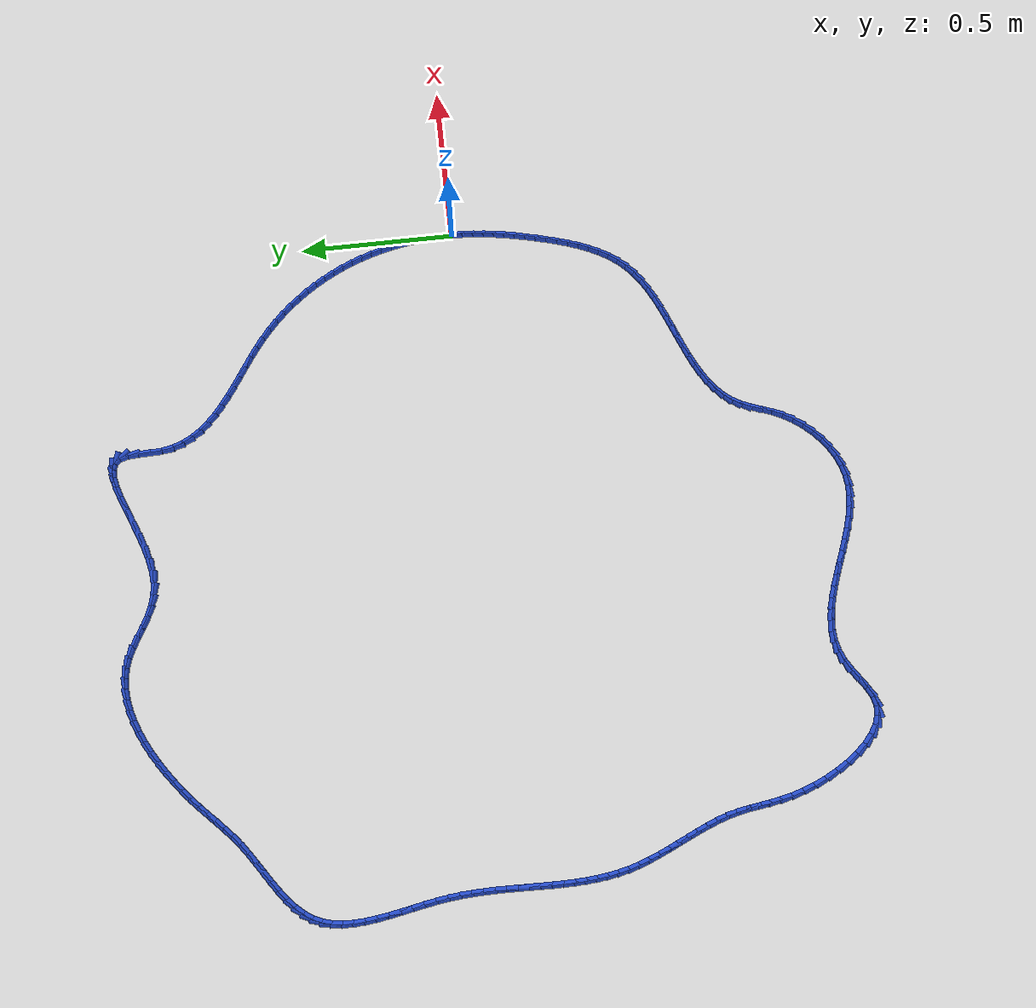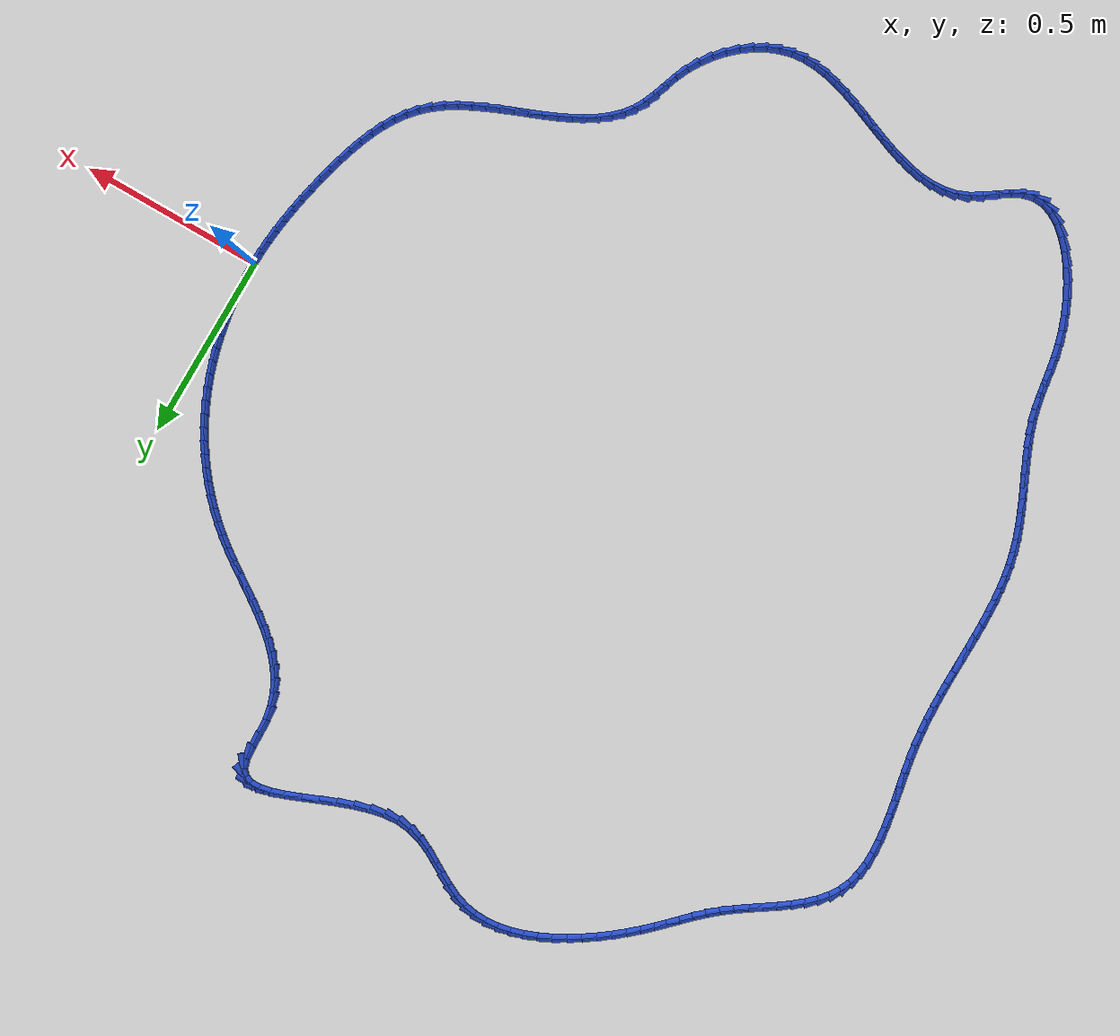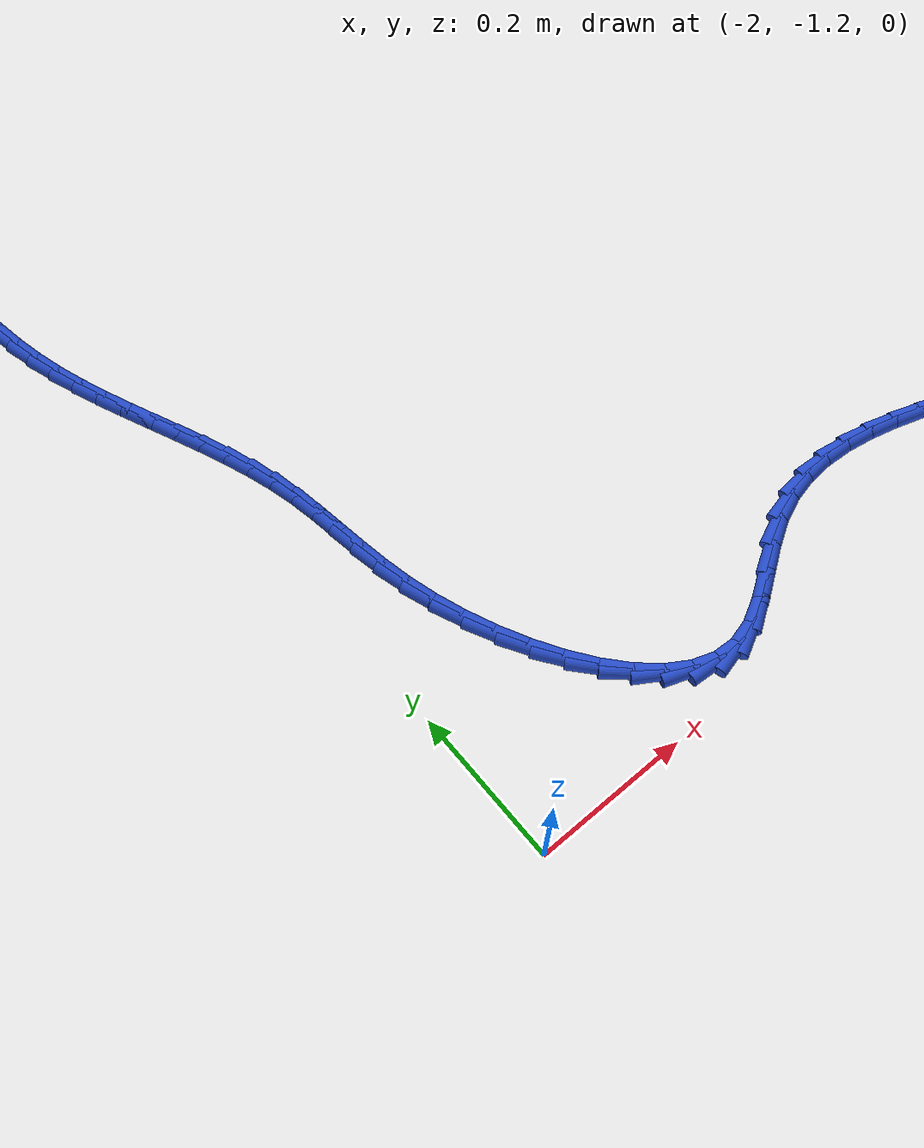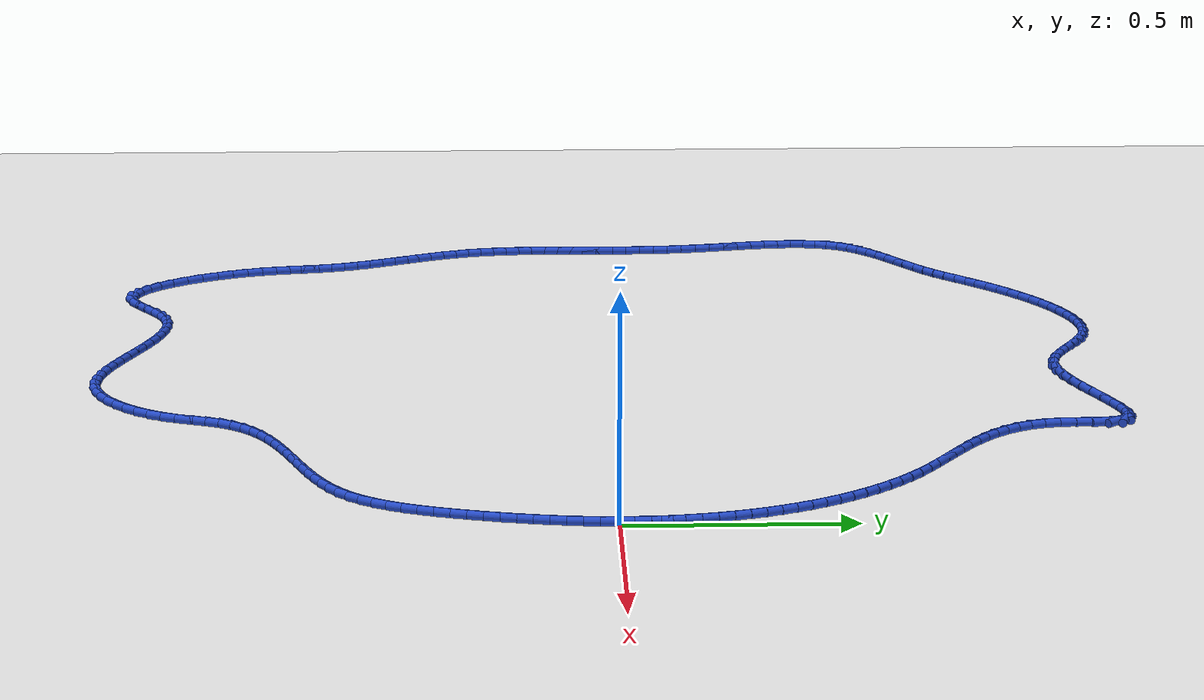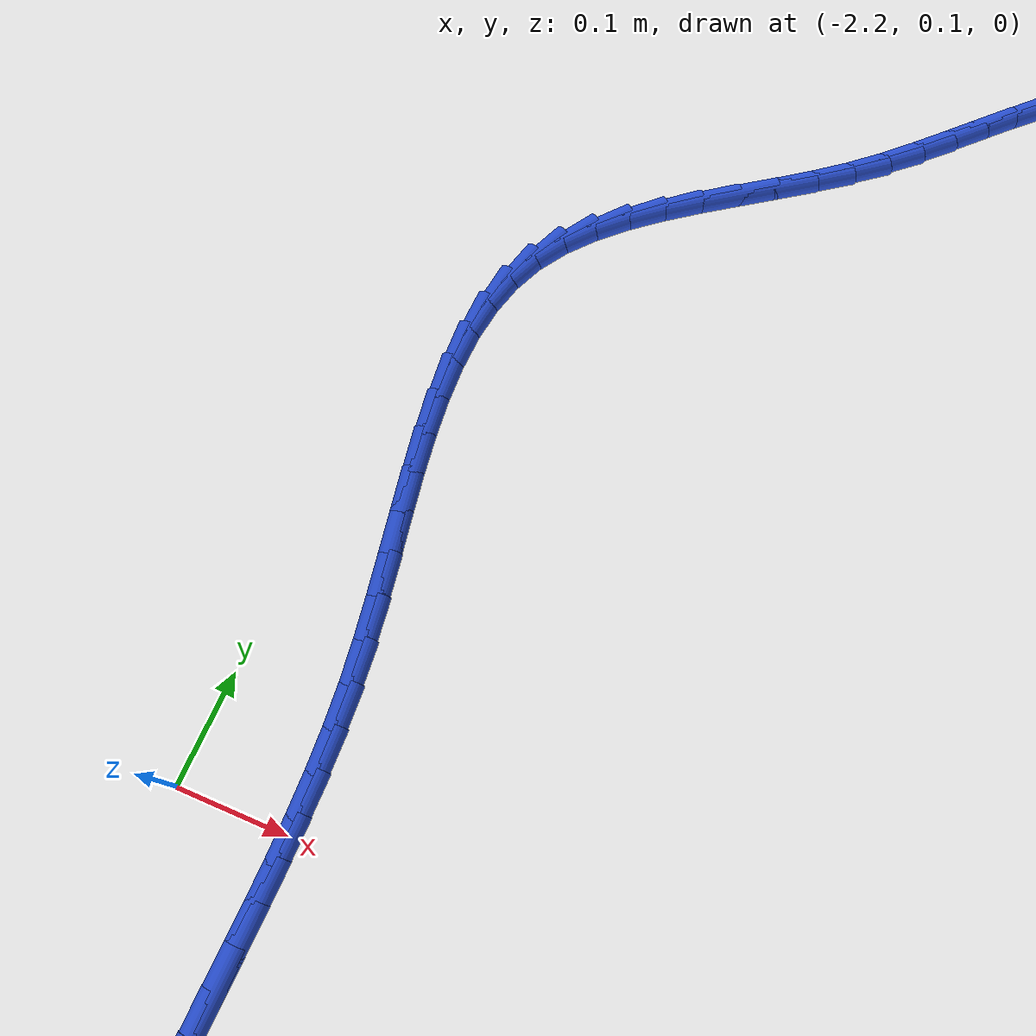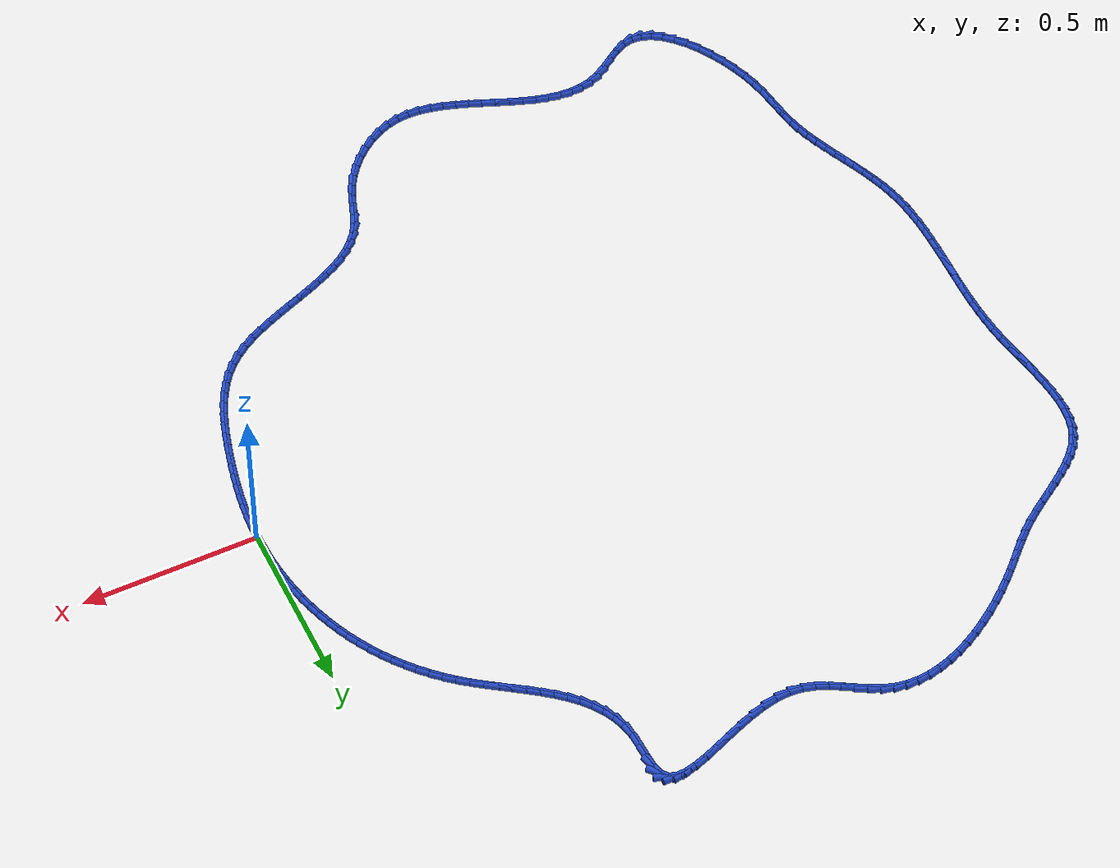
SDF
<sdf version="1.6">
 <world name="default">
  <light name="sun" type="directional">
   <pose>0 0 10 0 -0 0</pose>
   <diffuse>0.8 0.8 0.8 1</diffuse>
   <specular>0.2 0.2 0.2 1</specular>
   <attenuation>
    <range>1000</range>
    <constant>0.9</constant>
    <linear>0.01</linear>
    <quadratic>0.001</quadratic>
   </attenuation>
   <direction>-0.5 0.1 -0.9</direction>
  </light>
  <model name="ground_plane">
   <static>1</static>
   <link name="link">
    <collision name="collision">
     <geometry><plane><normal>0 0 1</normal><size>100 100</size></plane></geometry>
     <surface><friction><ode><mu>100</mu><mu2>50</mu2></ode></friction></surface>
    </collision>
    <visual name="visual">
     <cast_shadows>0</cast_shadows>
     <geometry><plane><normal>0 0 1</normal><size>100 100</size></plane></geometry>
     <material>
      <script><uri>file://media/materials/scripts/gazebo.material</uri><name>Gazebo/WhiteGlow</name></script>
     </material>
    </visual>
   </link>
  </model>
  <gravity>0 0 -9.8</gravity>
  <magnetic_field>6e-06 2.3e-05 -4.2e-05</magnetic_field>
  <atmosphere type="adiabatic"/>
  <physics name="default_physics" default="0" type="ode">
   <max_step_size>0.001</max_step_size>
   <real_time_factor>1</real_time_factor>
   <real_time_update_rate>1000</real_time_update_rate>
  </physics>
  <scene><ambient>0.4 0.4 0.4 1</ambient><background>0.7 0.7 0.7 1</background><shadows>1</shadows></scene>
  <spherical_coordinates>
   <surface_model>EARTH_WGS84</surface_model>
   <latitude_deg>0</latitude_deg>
   <longitude_deg>0</longitude_deg>
   <elevation>0</elevation>
   <heading_deg>0</heading_deg>
  </spherical_coordinates>
  <model name="line">
   <link name="link_0">
    <pose>-2.5153490401663703e-17 9.020562075079397e-17 0.01 0 1.57 -1.566581821676759</pose>
    <collision name="collision">
     <geometry><cylinder><radius>0.01</radius><length>0.08</length></cylinder></geometry>
    </collision>
    <visual name="visual">
     <material>
      <script><name>Gazebo/Blue</name><uri>file://media/materials/scripts/gazebo.material</uri></script>
     </material>
     <geometry><cylinder><radius>0.01</radius><length>0.08</length></cylinder></geometry>
    </visual>
   </link>
   <link name="link_1">
    <pose>-0.00014618991644907046 0.034687121454547734 0.01 0 1.57 -1.5289425890424635</pose>
    <collision name="collision">
     <geometry><cylinder><radius>0.01</radius><length>0.08</length></cylinder></geometry>
    </collision>
    <visual name="visual">
     <material>
      <script><name>Gazebo/Blue</name><uri>file://media/materials/scripts/gazebo.material</uri></script>
     </material>
     <geometry><cylinder><radius>0.01</radius><length>0.08</length></cylinder></geometry>
    </visual>
   </link>
   <link name="link_2">
    <pose>-0.0016028432533281537 0.06947021989820973 0.01 0 1.57 -1.4912024418300496</pose>
    <collision name="collision">
     <geometry><cylinder><radius>0.01</radius><length>0.08</length></cylinder></geometry>
    </collision>
    <visual name="visual">
     <material>
      <script><name>Gazebo/Blue</name><uri>file://media/materials/scripts/gazebo.material</uri></script>
     </material>
     <geometry><cylinder><radius>0.01</radius><length>0.08</length></cylinder></geometry>
    </visual>
   </link>
   <link name="link_3">
    <pose>-0.004378318121980279 0.10426700538823463 0.01 0 1.57 -1.453205174928311</pose>
    <collision name="collision">
     <geometry><cylinder><radius>0.01</radius><length>0.08</length></cylinder></geometry>
    </collision>
    <visual name="visual">
     <material>
      <script><name>Gazebo/Blue</name><uri>file://media/materials/scripts/gazebo.material</uri></script>
     </material>
     <geometry><cylinder><radius>0.01</radius><length>0.08</length></cylinder></geometry>
    </visual>
   </link>
   <link name="link_4">
    <pose>-0.00848097263374845 0.138995187981871 0.01 0 1.57 -1.4147977861607879</pose>
    <collision name="collision">
     <geometry><cylinder><radius>0.01</radius><length>0.08</length></cylinder></geometry>
    </collision>
    <visual name="visual">
     <material>
      <script><name>Gazebo/Blue</name><uri>file://media/materials/scripts/gazebo.material</uri></script>
     </material>
     <geometry><cylinder><radius>0.01</radius><length>0.08</length></cylinder></geometry>
    </visual>
   </link>
   <link name="link_5">
    <pose>-0.013919164899975668 0.17357247773636725 0.01 0 1.57 -1.3758302296160616</pose>
    <collision name="collision">
     <geometry><cylinder><radius>0.01</radius><length>0.08</length></cylinder></geometry>
    </collision>
    <visual name="visual">
     <material>
      <script><name>Gazebo/Blue</name><uri>file://media/materials/scripts/gazebo.material</uri></script>
     </material>
     <geometry><cylinder><radius>0.01</radius><length>0.08</length></cylinder></geometry>
    </visual>
   </link>
   <link name="link_6">
    <pose>-0.020701253032004947 0.20791658470897217 0.01 0 1.57 -1.3361554402698805</pose>
    <collision name="collision">
     <geometry><cylinder><radius>0.01</radius><length>0.08</length></cylinder></geometry>
    </collision>
    <visual name="visual">
     <material>
      <script><name>Gazebo/Blue</name><uri>file://media/materials/scripts/gazebo.material</uri></script>
     </material>
     <geometry><cylinder><radius>0.01</radius><length>0.08</length></cylinder></geometry>
    </visual>
   </link>
   <link name="link_7">
    <pose>-0.028835595141179296 0.24194521895693413 0.01 0 1.57 -1.2956296958626436</pose>
    <collision name="collision">
     <geometry><cylinder><radius>0.01</radius><length>0.08</length></cylinder></geometry>
    </collision>
    <visual name="visual">
     <material>
      <script><name>Gazebo/Blue</name><uri>file://media/materials/scripts/gazebo.material</uri></script>
     </material>
     <geometry><cylinder><radius>0.01</radius><length>0.08</length></cylinder></geometry>
    </visual>
   </link>
   <link name="link_8">
    <pose>-0.03833054933884168 0.27557609053750165 0.01 0 1.57 -1.254119709960961</pose>
    <collision name="collision">
     <geometry><cylinder><radius>0.01</radius><length>0.08</length></cylinder></geometry>
    </collision>
    <visual name="visual">
     <material>
      <script><name>Gazebo/Blue</name><uri>file://media/materials/scripts/gazebo.material</uri></script>
     </material>
     <geometry><cylinder><radius>0.01</radius><length>0.08</length></cylinder></geometry>
    </visual>
   </link>
   <link name="link_9">
    <pose>-0.049194401081264896 0.30872739603644345 0.01 0 1.57 -1.211726273923208</pose>
    <collision name="collision">
     <geometry><cylinder><radius>0.01</radius><length>0.08</length></cylinder></geometry>
    </collision>
    <visual name="visual">
     <material>
      <script><name>Gazebo/Blue</name><uri>file://media/materials/scripts/gazebo.material</uri></script>
     </material>
     <geometry><cylinder><radius>0.01</radius><length>0.08</length></cylinder></geometry>
    </visual>
   </link>
   <link name="link_10">
    <pose>-0.06143296571920128 0.3413338728917935 0.01 0 1.57 -1.1686869872502963</pose>
    <collision name="collision">
     <geometry><cylinder><radius>0.01</radius><length>0.08</length></cylinder></geometry>
    </collision>
    <visual name="visual">
     <material>
      <script><name>Gazebo/Blue</name><uri>file://media/materials/scripts/gazebo.material</uri></script>
     </material>
     <geometry><cylinder><radius>0.01</radius><length>0.08</length></cylinder></geometry>
    </visual>
   </link>
   <link name="link_11">
    <pose>-0.07504904100723751 0.37335046561855495 0.01 0 1.57 -1.125028070891858</pose>
    <collision name="collision">
     <geometry><cylinder><radius>0.01</radius><length>0.08</length></cylinder></geometry>
    </collision>
    <visual name="visual">
     <material>
      <script><name>Gazebo/Blue</name><uri>file://media/materials/scripts/gazebo.material</uri></script>
     </material>
     <geometry><cylinder><radius>0.01</radius><length>0.08</length></cylinder></geometry>
    </visual>
   </link>
   <link name="link_12">
    <pose>-0.0900452411691731 0.4047333477300911 0.01 0 1.57 -1.0807691425282067</pose>
    <collision name="collision">
     <geometry><cylinder><radius>0.01</radius><length>0.08</length></cylinder></geometry>
    </collision>
    <visual name="visual">
     <material>
      <script><name>Gazebo/Blue</name><uri>file://media/materials/scripts/gazebo.material</uri></script>
     </material>
     <geometry><cylinder><radius>0.01</radius><length>0.08</length></cylinder></geometry>
    </visual>
   </link>
   <link name="link_13">
    <pose>-0.10642418042880772 0.4354386927397659 0.01 0 1.57 -1.035939811634155</pose>
    <collision name="collision">
     <geometry><cylinder><radius>0.01</radius><length>0.08</length></cylinder></geometry>
    </collision>
    <visual name="visual">
     <material>
      <script><name>Gazebo/Blue</name><uri>file://media/materials/scripts/gazebo.material</uri></script>
     </material>
     <geometry><cylinder><radius>0.01</radius><length>0.08</length></cylinder></geometry>
    </visual>
   </link>
   <link name="link_14">
    <pose>-0.124188473009941 0.465422674160943 0.01 0 1.57 -0.9905801278837809</pose>
    <collision name="collision">
     <geometry><cylinder><radius>0.01</radius><length>0.08</length></cylinder></geometry>
    </collision>
    <visual name="visual">
     <material>
      <script><name>Gazebo/Blue</name><uri>file://media/materials/scripts/gazebo.material</uri></script>
     </material>
     <geometry><cylinder><radius>0.01</radius><length>0.08</length></cylinder></geometry>
    </visual>
   </link>
   <link name="link_15">
    <pose>-0.1433407331363724 0.494641465506986 0.01 0 1.57 -0.9447408046540455</pose>
    <collision name="collision">
     <geometry><cylinder><radius>0.01</radius><length>0.08</length></cylinder></geometry>
    </collision>
    <visual name="visual">
     <material>
      <script><name>Gazebo/Blue</name><uri>file://media/materials/scripts/gazebo.material</uri></script>
     </material>
     <geometry><cylinder><radius>0.01</radius><length>0.08</length></cylinder></geometry>
    </visual>
   </link>
   <link name="link_16">
    <pose>-0.16388357503190154 0.5230512402912586 0.01 0 1.57 -0.8984831738414026</pose>
    <collision name="collision">
     <geometry><cylinder><radius>0.01</radius><length>0.08</length></cylinder></geometry>
    </collision>
    <visual name="visual">
     <material>
      <script><name>Gazebo/Blue</name><uri>file://media/materials/scripts/gazebo.material</uri></script>
     </material>
     <geometry><cylinder><radius>0.01</radius><length>0.08</length></cylinder></geometry>
    </visual>
   </link>
   <link name="link_17">
    <pose>-0.18581961292032811 0.5506081720271246 0.01 0 1.57 -0.8518788364810641</pose>
    <collision name="collision">
     <geometry><cylinder><radius>0.01</radius><length>0.08</length></cylinder></geometry>
    </collision>
    <visual name="visual">
     <material>
      <script><name>Gazebo/Blue</name><uri>file://media/materials/scripts/gazebo.material</uri></script>
     </material>
     <geometry><cylinder><radius>0.01</radius><length>0.08</length></cylinder></geometry>
    </visual>
   </link>
   <link name="link_18">
    <pose>-0.20915146102545157 0.5772684342279475 0.01 0 1.57 -0.8050089864482842</pose>
    <collision name="collision">
     <geometry><cylinder><radius>0.01</radius><length>0.08</length></cylinder></geometry>
    </collision>
    <visual name="visual">
     <material>
      <script><name>Gazebo/Blue</name><uri>file://media/materials/scripts/gazebo.material</uri></script>
     </material>
     <geometry><cylinder><radius>0.01</radius><length>0.08</length></cylinder></geometry>
    </visual>
   </link>
   <link name="link_19">
    <pose>-0.23388173357107167 0.6029882004070912 0.01 0 1.57 -0.7579634013930133</pose>
    <collision name="collision">
     <geometry><cylinder><radius>0.01</radius><length>0.08</length></cylinder></geometry>
    </collision>
    <visual name="visual">
     <material>
      <script><name>Gazebo/Blue</name><uri>file://media/materials/scripts/gazebo.material</uri></script>
     </material>
     <geometry><cylinder><radius>0.01</radius><length>0.08</length></cylinder></geometry>
    </visual>
   </link>
   <link name="link_20">
    <pose>-0.2600130447809878 0.6277236440779193 0.01 0 1.57 -0.71083911494491</pose>
    <collision name="collision">
     <geometry><cylinder><radius>0.01</radius><length>0.08</length></cylinder></geometry>
    </collision>
    <visual name="visual">
     <material>
      <script><name>Gazebo/Blue</name><uri>file://media/materials/scripts/gazebo.material</uri></script>
     </material>
     <geometry><cylinder><radius>0.01</radius><length>0.08</length></cylinder></geometry>
    </visual>
   </link>
   <link name="link_21">
    <pose>-0.2875480088789996 0.6514309387537953 0.01 0 1.57 -0.6643515840784678</pose>
    <collision name="collision">
     <geometry><cylinder><radius>0.01</radius><length>0.08</length></cylinder></geometry>
    </collision>
    <visual name="visual">
     <material>
      <script><name>Gazebo/Blue</name><uri>file://media/materials/scripts/gazebo.material</uri></script>
     </material>
     <geometry><cylinder><radius>0.01</radius><length>0.08</length></cylinder></geometry>
    </visual>
   </link>
   <link name="link_22">
    <pose>-0.31647084819478766 0.6740804517627779 0.01 0 1.57 -0.6269630576750314</pose>
    <collision name="collision">
     <geometry><cylinder><radius>0.01</radius><length>0.08</length></cylinder></geometry>
    </collision>
    <visual name="visual">
     <material>
      <script><name>Gazebo/Blue</name><uri>file://media/materials/scripts/gazebo.material</uri></script>
     </material>
     <geometry><cylinder><radius>0.01</radius><length>0.08</length></cylinder></geometry>
    </visual>
   </link>
   <link name="link_23">
    <pose>-0.34650794613013647 0.695841535808761 0.01 0 1.57 -0.6042930348156507</pose>
    <collision name="collision">
     <geometry><cylinder><radius>0.01</radius><length>0.08</length></cylinder></geometry>
    </collision>
    <visual name="visual">
     <material>
      <script><name>Gazebo/Blue</name><uri>file://media/materials/scripts/gazebo.material</uri></script>
     </material>
     <geometry><cylinder><radius>0.01</radius><length>0.08</length></cylinder></geometry>
    </visual>
   </link>
   <link name="link_24">
    <pose>-0.3771957205392337 0.7170301481684748 0.01 0 1.57 -0.5959263366896604</pose>
    <collision name="collision">
     <geometry><cylinder><radius>0.01</radius><length>0.08</length></cylinder></geometry>
    </collision>
    <visual name="visual">
     <material>
      <script><name>Gazebo/Blue</name><uri>file://media/materials/scripts/gazebo.material</uri></script>
     </material>
     <geometry><cylinder><radius>0.01</radius><length>0.08</length></cylinder></geometry>
    </visual>
   </link>
   <link name="link_25">
    <pose>-0.4080661704362095 0.7379656563273272 0.01 0 1.57 -0.6017209444932522</pose>
    <collision name="collision">
     <geometry><cylinder><radius>0.01</radius><length>0.08</length></cylinder></geometry>
    </collision>
    <visual name="visual">
     <material>
      <script><name>Gazebo/Blue</name><uri>file://media/materials/scripts/gazebo.material</uri></script>
     </material>
     <geometry><cylinder><radius>0.01</radius><length>0.08</length></cylinder></geometry>
    </visual>
   </link>
   <link name="link_26">
    <pose>-0.4386512948351944 0.7589674277707265 0.01 0 1.57 -0.622000265243973</pose>
    <collision name="collision">
     <geometry><cylinder><radius>0.01</radius><length>0.08</length></cylinder></geometry>
    </collision>
    <visual name="visual">
     <material>
      <script><name>Gazebo/Blue</name><uri>file://media/materials/scripts/gazebo.material</uri></script>
     </material>
     <geometry><cylinder><radius>0.01</radius><length>0.08</length></cylinder></geometry>
    </visual>
   </link>
   <link name="link_27">
    <pose>-0.4684830927503188 0.780354829984081 0.01 0 1.57 -0.6575451356810288</pose>
    <collision name="collision">
     <geometry><cylinder><radius>0.01</radius><length>0.08</length></cylinder></geometry>
    </collision>
    <visual name="visual">
     <material>
      <script><name>Gazebo/Blue</name><uri>file://media/materials/scripts/gazebo.material</uri></script>
     </material>
     <geometry><cylinder><radius>0.01</radius><length>0.08</length></cylinder></geometry>
    </visual>
   </link>
   <link name="link_28">
    <pose>-0.49709356319571274 0.8024472304527982 0.01 0 1.57 -0.7095142828332632</pose>
    <collision name="collision">
     <geometry><cylinder><radius>0.01</radius><length>0.08</length></cylinder></geometry>
    </collision>
    <visual name="visual">
     <material>
      <script><name>Gazebo/Blue</name><uri>file://media/materials/scripts/gazebo.material</uri></script>
     </material>
     <geometry><cylinder><radius>0.01</radius><length>0.08</length></cylinder></geometry>
    </visual>
   </link>
   <link name="link_29">
    <pose>-0.5240147051855071 0.8255639966622869 0.01 0 1.57 -0.7792363855738176</pose>
    <collision name="collision">
     <geometry><cylinder><radius>0.01</radius><length>0.08</length></cylinder></geometry>
    </collision>
    <visual name="visual">
     <material>
      <script><name>Gazebo/Blue</name><uri>file://media/materials/scripts/gazebo.material</uri></script>
     </material>
     <geometry><cylinder><radius>0.01</radius><length>0.08</length></cylinder></geometry>
    </visual>
   </link>
   <link name="link_30">
    <pose>-0.5487785177338318 0.8500244960979546 0.01 0 1.57 -0.8677837048059173</pose>
    <collision name="collision">
     <geometry><cylinder><radius>0.01</radius><length>0.08</length></cylinder></geometry>
    </collision>
    <visual name="visual">
     <material>
      <script><name>Gazebo/Blue</name><uri>file://media/materials/scripts/gazebo.material</uri></script>
     </material>
     <geometry><cylinder><radius>0.01</radius><length>0.08</length></cylinder></geometry>
    </visual>
   </link>
   <link name="link_31">
    <pose>-0.5709169998548174 0.8761480962452101 0.01 0 1.57 -0.9752509637494551</pose>
    <collision name="collision">
     <geometry><cylinder><radius>0.01</radius><length>0.08</length></cylinder></geometry>
    </collision>
    <visual name="visual">
     <material>
      <script><name>Gazebo/Blue</name><uri>file://media/materials/scripts/gazebo.material</uri></script>
     </material>
     <geometry><cylinder><radius>0.01</radius><length>0.08</length></cylinder></geometry>
    </visual>
   </link>
   <link name="link_32">
    <pose>-0.5899621505625945 0.904254164589461 0.01 0 1.57 -1.099812868632254</pose>
    <collision name="collision">
     <geometry><cylinder><radius>0.01</radius><length>0.08</length></cylinder></geometry>
    </collision>
    <visual name="visual">
     <material>
      <script><name>Gazebo/Blue</name><uri>file://media/materials/scripts/gazebo.material</uri></script>
     </material>
     <geometry><cylinder><radius>0.01</radius><length>0.08</length></cylinder></geometry>
    </visual>
   </link>
   <link name="link_33">
    <pose>-0.6054459688712931 0.9346620686161153 0.01 0 1.57 -1.236975381873383</pose>
    <collision name="collision">
     <geometry><cylinder><radius>0.01</radius><length>0.08</length></cylinder></geometry>
    </collision>
    <visual name="visual">
     <material>
      <script><name>Gazebo/Blue</name><uri>file://media/materials/scripts/gazebo.material</uri></script>
     </material>
     <geometry><cylinder><radius>0.01</radius><length>0.08</length></cylinder></geometry>
    </visual>
   </link>
   <link name="link_34">
    <pose>-0.6169004537950441 0.967691175810582 0.01 0 1.57 -1.3797373750186677</pose>
    <collision name="collision">
     <geometry><cylinder><radius>0.01</radius><length>0.08</length></cylinder></geometry>
    </collision>
    <visual name="visual">
     <material>
      <script><name>Gazebo/Blue</name><uri>file://media/materials/scripts/gazebo.material</uri></script>
     </material>
     <geometry><cylinder><radius>0.01</radius><length>0.08</length></cylinder></geometry>
    </visual>
   </link>
   <link name="link_35">
    <pose>-0.623857636709132 1.003660818817155 0.01 0 1.57 -1.5017482478699014</pose>
    <collision name="collision">
     <geometry><cylinder><radius>0.01</radius><length>0.08</length></cylinder></geometry>
    </collision>
    <visual name="visual">
     <material>
      <script><name>Gazebo/Blue</name><uri>file://media/materials/scripts/gazebo.material</uri></script>
     </material>
     <geometry><cylinder><radius>0.01</radius><length>0.08</length></cylinder></geometry>
    </visual>
   </link>
   <link name="link_36">
    <pose>-0.6265206996302933 1.042167746803596 0.01 0 1.57 -1.5453269639691765</pose>
    <collision name="collision">
     <geometry><cylinder><radius>0.01</radius><length>0.08</length></cylinder></geometry>
    </collision>
    <visual name="visual">
     <material>
      <script><name>Gazebo/Blue</name><uri>file://media/materials/scripts/gazebo.material</uri></script>
     </material>
     <geometry><cylinder><radius>0.01</radius><length>0.08</length></cylinder></geometry>
    </visual>
   </link>
   <link name="link_37">
    <pose>-0.6274902679781769 1.080227540297017 0.01 0 1.57 -1.5000875965602773</pose>
    <collision name="collision">
     <geometry><cylinder><radius>0.01</radius><length>0.08</length></cylinder></geometry>
    </collision>
    <visual name="visual">
     <material>
      <script><name>Gazebo/Blue</name><uri>file://media/materials/scripts/gazebo.material</uri></script>
     </material>
     <geometry><cylinder><radius>0.01</radius><length>0.08</length></cylinder></geometry>
    </visual>
   </link>
   <link name="link_38">
    <pose>-0.6299020715095869 1.1142796683998075 0.01 0 1.57 -1.3127866502357155</pose>
    <collision name="collision">
     <geometry><cylinder><radius>0.01</radius><length>0.08</length></cylinder></geometry>
    </collision>
    <visual name="visual">
     <material>
      <script><name>Gazebo/Blue</name><uri>file://media/materials/scripts/gazebo.material</uri></script>
     </material>
     <geometry><cylinder><radius>0.01</radius><length>0.08</length></cylinder></geometry>
    </visual>
   </link>
   <link name="link_39">
    <pose>-0.6368911775533318 1.1407644404582313 0.01 0 1.57 -0.872542147429926</pose>
    <collision name="collision">
     <geometry><cylinder><radius>0.01</radius><length>0.08</length></cylinder></geometry>
    </collision>
    <visual name="visual">
     <material>
      <script><name>Gazebo/Blue</name><uri>file://media/materials/scripts/gazebo.material</uri></script>
     </material>
     <geometry><cylinder><radius>0.01</radius><length>0.08</length></cylinder></geometry>
    </visual>
   </link>
   <link name="link_40">
    <pose>-0.6507151930627414 1.1572351633229339 0.01 0 1.57 -0.3457710219645095</pose>
    <collision name="collision">
     <geometry><cylinder><radius>0.01</radius><length>0.08</length></cylinder></geometry>
    </collision>
    <visual name="visual">
     <material>
      <script><name>Gazebo/Blue</name><uri>file://media/materials/scripts/gazebo.material</uri></script>
     </material>
     <geometry><cylinder><radius>0.01</radius><length>0.08</length></cylinder></geometry>
    </visual>
   </link>
   <link name="link_41">
    <pose>-0.6710249732802287 1.1645516272253162 0.01 0 1.57 0.014126392369307286</pose>
    <collision name="collision">
     <geometry><cylinder><radius>0.01</radius><length>0.08</length></cylinder></geometry>
    </collision>
    <visual name="visual">
     <material>
      <script><name>Gazebo/Blue</name><uri>file://media/materials/scripts/gazebo.material</uri></script>
     </material>
     <geometry><cylinder><radius>0.01</radius><length>0.08</length></cylinder></geometry>
    </visual>
   </link>
   <link name="link_42">
    <pose>-0.696989522038674 1.1641848174219658 0.01 0 1.57 0.21052189841606794</pose>
    <collision name="collision">
     <geometry><cylinder><radius>0.01</radius><length>0.08</length></cylinder></geometry>
    </collision>
    <visual name="visual">
     <material>
      <script><name>Gazebo/Blue</name><uri>file://media/materials/scripts/gazebo.material</uri></script>
     </material>
     <geometry><cylinder><radius>0.01</radius><length>0.08</length></cylinder></geometry>
    </visual>
   </link>
   <link name="link_43">
    <pose>-0.7277778431709583 1.1576057191694713 0.01 0 1.57 0.3146620787737415</pose>
    <collision name="collision">
     <geometry><cylinder><radius>0.01</radius><length>0.08</length></cylinder></geometry>
    </collision>
    <visual name="visual">
     <material>
      <script><name>Gazebo/Blue</name><uri>file://media/materials/scripts/gazebo.material</uri></script>
     </material>
     <geometry><cylinder><radius>0.01</radius><length>0.08</length></cylinder></geometry>
    </visual>
   </link>
   <link name="link_44">
    <pose>-0.762558940509962 1.1462853177244214 0.01 0 1.57 0.36711195769859556</pose>
    <collision name="collision">
     <geometry><cylinder><radius>0.01</radius><length>0.08</length></cylinder></geometry>
    </collision>
    <visual name="visual">
     <material>
      <script><name>Gazebo/Blue</name><uri>file://media/materials/scripts/gazebo.material</uri></script>
     </material>
     <geometry><cylinder><radius>0.01</radius><length>0.08</length></cylinder></geometry>
    </visual>
   </link>
   <link name="link_45">
    <pose>-0.8005018178885651 1.131694598343404 0.01 0 1.57 0.3864979659915495</pose>
    <collision name="collision">
     <geometry><cylinder><radius>0.01</radius><length>0.08</length></cylinder></geometry>
    </collision>
    <visual name="visual">
     <material>
      <script><name>Gazebo/Blue</name><uri>file://media/materials/scripts/gazebo.material</uri></script>
     </material>
     <geometry><cylinder><radius>0.01</radius><length>0.08</length></cylinder></geometry>
    </visual>
   </link>
   <link name="link_46">
    <pose>-0.8407754791396487 1.1153045462830076 0.01 0 1.57 0.38069250484605854</pose>
    <collision name="collision">
     <geometry><cylinder><radius>0.01</radius><length>0.08</length></cylinder></geometry>
    </collision>
    <visual name="visual">
     <material>
      <script><name>Gazebo/Blue</name><uri>file://media/materials/scripts/gazebo.material</uri></script>
     </material>
     <geometry><cylinder><radius>0.01</radius><length>0.08</length></cylinder></geometry>
    </visual>
   </link>
   <link name="link_47">
    <pose>-0.882548928096093 1.0985861467998201 0.01 0 1.57 0.3517273662462048</pose>
    <collision name="collision">
     <geometry><cylinder><radius>0.01</radius><length>0.08</length></cylinder></geometry>
    </collision>
    <visual name="visual">
     <material>
      <script><name>Gazebo/Blue</name><uri>file://media/materials/scripts/gazebo.material</uri></script>
     </material>
     <geometry><cylinder><radius>0.01</radius><length>0.08</length></cylinder></geometry>
    </visual>
   </link>
   <link name="link_48">
    <pose>-0.9249911685907786 1.08301038515043 0.01 0 1.57 0.29748088809117124</pose>
    <collision name="collision">
     <geometry><cylinder><radius>0.01</radius><length>0.08</length></cylinder></geometry>
    </collision>
    <visual name="visual">
     <material>
      <script><name>Gazebo/Blue</name><uri>file://media/materials/scripts/gazebo.material</uri></script>
     </material>
     <geometry><cylinder><radius>0.01</radius><length>0.08</length></cylinder></geometry>
    </visual>
   </link>
   <link name="link_49">
    <pose>-0.9672712044565863 1.0700482465914258 0.01 0 1.57 0.21179608505710049</pose>
    <collision name="collision">
     <geometry><cylinder><radius>0.01</radius><length>0.08</length></cylinder></geometry>
    </collision>
    <visual name="visual">
     <material>
      <script><name>Gazebo/Blue</name><uri>file://media/materials/scripts/gazebo.material</uri></script>
     </material>
     <geometry><cylinder><radius>0.01</radius><length>0.08</length></cylinder></geometry>
    </visual>
   </link>
   <link name="link_50">
    <pose>-1.0085580395263958 1.0611707163793958 0.01 0 1.57 0.08398128909818635</pose>
    <collision name="collision">
     <geometry><cylinder><radius>0.01</radius><length>0.08</length></cylinder></geometry>
    </collision>
    <visual name="visual">
     <material>
      <script><name>Gazebo/Blue</name><uri>file://media/materials/scripts/gazebo.material</uri></script>
     </material>
     <geometry><cylinder><radius>0.01</radius><length>0.08</length></cylinder></geometry>
    </visual>
   </link>
   <link name="link_51">
    <pose>-1.0480206776330891 1.0578487797709282 0.01 0 1.57 -0.09417309541365061</pose>
    <collision name="collision">
     <geometry><cylinder><radius>0.01</radius><length>0.08</length></cylinder></geometry>
    </collision>
    <visual name="visual">
     <material>
      <script><name>Gazebo/Blue</name><uri>file://media/materials/scripts/gazebo.material</uri></script>
     </material>
     <geometry><cylinder><radius>0.01</radius><length>0.08</length></cylinder></geometry>
    </visual>
   </link>
   <link name="link_52">
    <pose>-1.0849230172846445 1.061334297275301 0.01 0 1.57 -0.2718660057260044</pose>
    <collision name="collision">
     <geometry><cylinder><radius>0.01</radius><length>0.08</length></cylinder></geometry>
    </collision>
    <visual name="visual">
     <material>
      <script><name>Gazebo/Blue</name><uri>file://media/materials/scripts/gazebo.material</uri></script>
     </material>
     <geometry><cylinder><radius>0.01</radius><length>0.08</length></cylinder></geometry>
    </visual>
   </link>
   <link name="link_53">
    <pose>-1.1193700111600657 1.0709370206111122 0.01 0 1.57 -0.4067246753438625</pose>
    <collision name="collision">
     <geometry><cylinder><radius>0.01</radius><length>0.08</length></cylinder></geometry>
    </collision>
    <visual name="visual">
     <material>
      <script><name>Gazebo/Blue</name><uri>file://media/materials/scripts/gazebo.material</uri></script>
     </material>
     <geometry><cylinder><radius>0.01</radius><length>0.08</length></cylinder></geometry>
    </visual>
   </link>
   <link name="link_54">
    <pose>-1.151906158742915 1.0849517279762726 0.01 0 1.57 -0.4921197814711319</pose>
    <collision name="collision">
     <geometry><cylinder><radius>0.01</radius><length>0.08</length></cylinder></geometry>
    </collision>
    <visual name="visual">
     <material>
      <script><name>Gazebo/Blue</name><uri>file://media/materials/scripts/gazebo.material</uri></script>
     </material>
     <geometry><cylinder><radius>0.01</radius><length>0.08</length></cylinder></geometry>
    </visual>
   </link>
   <link name="link_55">
    <pose>-1.18307979044663 1.1016643514291158 0.01 0 1.57 -0.5277498516289822</pose>
    <collision name="collision">
     <geometry><cylinder><radius>0.01</radius><length>0.08</length></cylinder></geometry>
    </collision>
    <visual name="visual">
     <material>
      <script><name>Gazebo/Blue</name><uri>file://media/materials/scripts/gazebo.material</uri></script>
     </material>
     <geometry><cylinder><radius>0.01</radius><length>0.08</length></cylinder></geometry>
    </visual>
   </link>
   <link name="link_56">
    <pose>-1.2134392366846507 1.119360823027975 0.01 0 1.57 -0.5133634655075486</pose>
    <collision name="collision">
     <geometry><cylinder><radius>0.01</radius><length>0.08</length></cylinder></geometry>
    </collision>
    <visual name="visual">
     <material>
      <script><name>Gazebo/Blue</name><uri>file://media/materials/scripts/gazebo.material</uri></script>
     </material>
     <geometry><cylinder><radius>0.01</radius><length>0.08</length></cylinder></geometry>
    </visual>
   </link>
   <link name="link_57">
    <pose>-1.2435328278704143 1.1363270748311838 0.01 0 1.57 -0.4459522872256851</pose>
    <collision name="collision">
     <geometry><cylinder><radius>0.01</radius><length>0.08</length></cylinder></geometry>
    </collision>
    <visual name="visual">
     <material>
      <script><name>Gazebo/Blue</name><uri>file://media/materials/scripts/gazebo.material</uri></script>
     </material>
     <geometry><cylinder><radius>0.01</radius><length>0.08</length></cylinder></geometry>
    </visual>
   </link>
   <link name="link_58">
    <pose>-1.2739088944173609 1.1508490388970756 0.01 0 1.57 -0.322100916913649</pose>
    <collision name="collision">
     <geometry><cylinder><radius>0.01</radius><length>0.08</length></cylinder></geometry>
    </collision>
    <visual name="visual">
     <material>
      <script><name>Gazebo/Blue</name><uri>file://media/materials/scripts/gazebo.material</uri></script>
     </material>
     <geometry><cylinder><radius>0.01</radius><length>0.08</length></cylinder></geometry>
    </visual>
   </link>
   <link name="link_59">
    <pose>-1.305099322435715 1.1612579918295405 0.01 0 1.57 -0.17322972552930815</pose>
    <collision name="collision">
     <geometry><cylinder><radius>0.01</radius><length>0.08</length></cylinder></geometry>
    </collision>
    <visual name="visual">
     <material>
      <script><name>Gazebo/Blue</name><uri>file://media/materials/scripts/gazebo.material</uri></script>
     </material>
     <geometry><cylinder><radius>0.01</radius><length>0.08</length></cylinder></geometry>
    </visual>
   </link>
   <link name="link_60">
    <pose>-1.3372724225972956 1.166887755783767 0.01 0 1.57 -0.035322412318220336</pose>
    <collision name="collision">
     <geometry><cylinder><radius>0.01</radius><length>0.08</length></cylinder></geometry>
    </collision>
    <visual name="visual">
     <material>
      <script><name>Gazebo/Blue</name><uri>file://media/materials/scripts/gazebo.material</uri></script>
     </material>
     <geometry><cylinder><radius>0.01</radius><length>0.08</length></cylinder></geometry>
    </visual>
   </link>
   <link name="link_61">
    <pose>-1.3702408840202904 1.1680527659291147 0.01 0 1.57 0.0875055713214895</pose>
    <collision name="collision">
     <geometry><cylinder><radius>0.01</radius><length>0.08</length></cylinder></geometry>
    </collision>
    <visual name="visual">
     <material>
      <script><name>Gazebo/Blue</name><uri>file://media/materials/scripts/gazebo.material</uri></script>
     </material>
     <geometry><cylinder><radius>0.01</radius><length>0.08</length></cylinder></geometry>
    </visual>
   </link>
   <link name="link_62">
    <pose>-1.40380254254063 1.1651084148002613 0.01 0 1.57 0.194782580031764</pose>
    <collision name="collision">
     <geometry><cylinder><radius>0.01</radius><length>0.08</length></cylinder></geometry>
    </collision>
    <visual name="visual">
     <material>
      <script><name>Gazebo/Blue</name><uri>file://media/materials/scripts/gazebo.material</uri></script>
     </material>
     <geometry><cylinder><radius>0.01</radius><length>0.08</length></cylinder></geometry>
    </visual>
   </link>
   <link name="link_63">
    <pose>-1.4377552339942437 1.1584100949318827 0.01 0 1.57 0.2875404967684009</pose>
    <collision name="collision">
     <geometry><cylinder><radius>0.01</radius><length>0.08</length></cylinder></geometry>
    </collision>
    <visual name="visual">
     <material>
      <script><name>Gazebo/Blue</name><uri>file://media/materials/scripts/gazebo.material</uri></script>
     </material>
     <geometry><cylinder><radius>0.01</radius><length>0.08</length></cylinder></geometry>
    </visual>
   </link>
   <link name="link_64">
    <pose>-1.4718967942170615 1.148313198858657 0.01 0 1.57 0.3675266486257163</pose>
    <collision name="collision">
     <geometry><cylinder><radius>0.01</radius><length>0.08</length></cylinder></geometry>
    </collision>
    <visual name="visual">
     <material>
      <script><name>Gazebo/Blue</name><uri>file://media/materials/scripts/gazebo.material</uri></script>
     </material>
     <geometry><cylinder><radius>0.01</radius><length>0.08</length></cylinder></geometry>
    </visual>
   </link>
   <link name="link_65">
    <pose>-1.506025059045013 1.1351731191152608 0.01 0 1.57 0.4366730466395532</pose>
    <collision name="collision">
     <geometry><cylinder><radius>0.01</radius><length>0.08</length></cylinder></geometry>
    </collision>
    <visual name="visual">
     <material>
      <script><name>Gazebo/Blue</name><uri>file://media/materials/scripts/gazebo.material</uri></script>
     </material>
     <geometry><cylinder><radius>0.01</radius><length>0.08</length></cylinder></geometry>
    </visual>
   </link>
   <link name="link_66">
    <pose>-1.5399378643140285 1.1193452482363706 0.01 0 1.57 0.4968161380558348</pose>
    <collision name="collision">
     <geometry><cylinder><radius>0.01</radius><length>0.08</length></cylinder></geometry>
    </collision>
    <visual name="visual">
     <material>
      <script><name>Gazebo/Blue</name><uri>file://media/materials/scripts/gazebo.material</uri></script>
     </material>
     <geometry><cylinder><radius>0.01</radius><length>0.08</length></cylinder></geometry>
    </visual>
   </link>
   <link name="link_67">
    <pose>-1.573433045860037 1.101184978756664 0.01 0 1.57 0.5495842767975659</pose>
    <collision name="collision">
     <geometry><cylinder><radius>0.01</radius><length>0.08</length></cylinder></geometry>
    </collision>
    <visual name="visual">
     <material>
      <script><name>Gazebo/Blue</name><uri>file://media/materials/scripts/gazebo.material</uri></script>
     </material>
     <geometry><cylinder><radius>0.01</radius><length>0.08</length></cylinder></geometry>
    </visual>
   </link>
   <link name="link_68">
    <pose>-1.6063084395189688 1.0810477032108177 0.01 0 1.57 0.5963772638823972</pose>
    <collision name="collision">
     <geometry><cylinder><radius>0.01</radius><length>0.08</length></cylinder></geometry>
    </collision>
    <visual name="visual">
     <material>
      <script><name>Gazebo/Blue</name><uri>file://media/materials/scripts/gazebo.material</uri></script>
     </material>
     <geometry><cylinder><radius>0.01</radius><length>0.08</length></cylinder></geometry>
    </visual>
   </link>
   <link name="link_69">
    <pose>-1.6383618811267544 1.0592888141335082 0.01 0 1.57 0.6383894890014451</pose>
    <collision name="collision">
     <geometry><cylinder><radius>0.01</radius><length>0.08</length></cylinder></geometry>
    </collision>
    <visual name="visual">
     <material>
      <script><name>Gazebo/Blue</name><uri>file://media/materials/scripts/gazebo.material</uri></script>
     </material>
     <geometry><cylinder><radius>0.01</radius><length>0.08</length></cylinder></geometry>
    </visual>
   </link>
   <link name="link_70">
    <pose>-1.6693912065193213 1.0362637040594127 0.01 0 1.57 0.676651033779097</pose>
    <collision name="collision">
     <geometry><cylinder><radius>0.01</radius><length>0.08</length></cylinder></geometry>
    </collision>
    <visual name="visual">
     <material>
      <script><name>Gazebo/Blue</name><uri>file://media/materials/scripts/gazebo.material</uri></script>
     </material>
     <geometry><cylinder><radius>0.01</radius><length>0.08</length></cylinder></geometry>
    </visual>
   </link>
   <link name="link_71">
    <pose>-1.6991942515326013 1.0123277655232086 0.01 0 1.57 0.7120756807734522</pose>
    <collision name="collision">
     <geometry><cylinder><radius>0.01</radius><length>0.08</length></cylinder></geometry>
    </collision>
    <visual name="visual">
     <material>
      <script><name>Gazebo/Blue</name><uri>file://media/materials/scripts/gazebo.material</uri></script>
     </material>
     <geometry><cylinder><radius>0.01</radius><length>0.08</length></cylinder></geometry>
    </visual>
   </link>
   <link name="link_72">
    <pose>-1.7275688520025239 0.9878363910595723 0.01 0 1.57 0.7453831184641909</pose>
    <collision name="collision">
     <geometry><cylinder><radius>0.01</radius><length>0.08</length></cylinder></geometry>
    </collision>
    <visual name="visual">
     <material>
      <script><name>Gazebo/Blue</name><uri>file://media/materials/scripts/gazebo.material</uri></script>
     </material>
     <geometry><cylinder><radius>0.01</radius><length>0.08</length></cylinder></geometry>
    </visual>
   </link>
   <link name="link_73">
    <pose>-1.7543216307839666 0.9631433197362219 0.01 0 1.57 0.7713417953977889</pose>
    <collision name="collision">
     <geometry><cylinder><radius>0.01</radius><length>0.08</length></cylinder></geometry>
    </collision>
    <visual name="visual">
     <material>
      <script><name>Gazebo/Blue</name><uri>file://media/materials/scripts/gazebo.material</uri></script>
     </material>
     <geometry><cylinder><radius>0.01</radius><length>0.08</length></cylinder></geometry>
    </visual>
   </link>
   <link name="link_74">
    <pose>-1.779635232296701 0.9385315340608751 0.01 0 1.57 0.7808372961791213</pose>
    <collision name="collision">
     <geometry><cylinder><radius>0.01</radius><length>0.08</length></cylinder></geometry>
    </collision>
    <visual name="visual">
     <material>
      <script><name>Gazebo/Blue</name><uri>file://media/materials/scripts/gazebo.material</uri></script>
     </material>
     <geometry><cylinder><radius>0.01</radius><length>0.08</length></cylinder></geometry>
    </visual>
   </link>
   <link name="link_75">
    <pose>-1.8042016715444495 0.9141881674898916 0.01 0 1.57 0.7719212531692389</pose>
    <collision name="collision">
     <geometry><cylinder><radius>0.01</radius><length>0.08</length></cylinder></geometry>
    </collision>
    <visual name="visual">
     <material>
      <script><name>Gazebo/Blue</name><uri>file://media/materials/scripts/gazebo.material</uri></script>
     </material>
     <geometry><cylinder><radius>0.01</radius><length>0.08</length></cylinder></geometry>
    </visual>
   </link>
   <link name="link_76">
    <pose>-1.8287491929784072 0.8902935361284101 0.01 0 1.57 0.744383082709051</pose>
    <collision name="collision">
     <geometry><cylinder><radius>0.01</radius><length>0.08</length></cylinder></geometry>
    </collision>
    <visual name="visual">
     <material>
      <script><name>Gazebo/Blue</name><uri>file://media/materials/scripts/gazebo.material</uri></script>
     </material>
     <geometry><cylinder><radius>0.01</radius><length>0.08</length></cylinder></geometry>
    </visual>
   </link>
   <link name="link_77">
    <pose>-1.8540060410497685 0.8670279560815712 0.01 0 1.57 0.6993820109860589</pose>
    <collision name="collision">
     <geometry><cylinder><radius>0.01</radius><length>0.08</length></cylinder></geometry>
    </collision>
    <visual name="visual">
     <material>
      <script><name>Gazebo/Blue</name><uri>file://media/materials/scripts/gazebo.material</uri></script>
     </material>
     <geometry><cylinder><radius>0.01</radius><length>0.08</length></cylinder></geometry>
    </visual>
   </link>
   <link name="link_78">
    <pose>-1.8807004597273815 0.8445717432866604 0.01 0 1.57 0.6459647797703112</pose>
    <collision name="collision">
     <geometry><cylinder><radius>0.01</radius><length>0.08</length></cylinder></geometry>
    </collision>
    <visual name="visual">
     <material>
      <script><name>Gazebo/Blue</name><uri>file://media/materials/scripts/gazebo.material</uri></script>
     </material>
     <geometry><cylinder><radius>0.01</radius><length>0.08</length></cylinder></geometry>
    </visual>
   </link>
   <link name="link_79">
    <pose>-1.9092975464011002 0.8230136401910809 0.01 0 1.57 0.6098002822050382</pose>
    <collision name="collision">
     <geometry><cylinder><radius>0.01</radius><length>0.08</length></cylinder></geometry>
    </collision>
    <visual name="visual">
     <material>
      <script><name>Gazebo/Blue</name><uri>file://media/materials/scripts/gazebo.material</uri></script>
     </material>
     <geometry><cylinder><radius>0.01</radius><length>0.08</length></cylinder></geometry>
    </visual>
   </link>
   <link name="link_80">
    <pose>-1.9392482113033065 0.8020894579681237 0.01 0 1.57 0.5947539697306149</pose>
    <collision name="collision">
     <geometry><cylinder><radius>0.01</radius><length>0.08</length></cylinder></geometry>
    </collision>
    <visual name="visual">
     <material>
      <script><name>Gazebo/Blue</name><uri>file://media/materials/scripts/gazebo.material</uri></script>
     </material>
     <geometry><cylinder><radius>0.01</radius><length>0.08</length></cylinder></geometry>
    </visual>
   </link>
   <link name="link_81">
    <pose>-1.96975906994291 0.7814499946380539 0.01 0 1.57 0.5997722727494126</pose>
    <collision name="collision">
     <geometry><cylinder><radius>0.01</radius><length>0.08</length></cylinder></geometry>
    </collision>
    <visual name="visual">
     <material>
      <script><name>Gazebo/Blue</name><uri>file://media/materials/scripts/gazebo.material</uri></script>
     </material>
     <geometry><cylinder><radius>0.01</radius><length>0.08</length></cylinder></geometry>
    </visual>
   </link>
   <link name="link_82">
    <pose>-2.000036737828821 0.760746048221136 0.01 0 1.57 0.6253017335344195</pose>
    <collision name="collision">
     <geometry><cylinder><radius>0.01</radius><length>0.08</length></cylinder></geometry>
    </collision>
    <visual name="visual">
     <material>
      <script><name>Gazebo/Blue</name><uri>file://media/materials/scripts/gazebo.material</uri></script>
     </material>
     <geometry><cylinder><radius>0.01</radius><length>0.08</length></cylinder></geometry>
    </visual>
   </link>
   <link name="link_83">
    <pose>-2.029287830469948 0.7396284167376357 0.01 0 1.57 0.6733080510367261</pose>
    <collision name="collision">
     <geometry><cylinder><radius>0.01</radius><length>0.08</length></cylinder></geometry>
    </collision>
    <visual name="visual">
     <material>
      <script><name>Gazebo/Blue</name><uri>file://media/materials/scripts/gazebo.material</uri></script>
     </material>
     <geometry><cylinder><radius>0.01</radius><length>0.08</length></cylinder></geometry>
    </visual>
   </link>
   <link name="link_84">
    <pose>-2.056718963375199 0.7177478982078175 0.01 0 1.57 0.7472412897648841</pose>
    <collision name="collision">
     <geometry><cylinder><radius>0.01</radius><length>0.08</length></cylinder></geometry>
    </collision>
    <visual name="visual">
     <material>
      <script><name>Gazebo/Blue</name><uri>file://media/materials/scripts/gazebo.material</uri></script>
     </material>
     <geometry><cylinder><radius>0.01</radius><length>0.08</length></cylinder></geometry>
    </visual>
   </link>
   <link name="link_85">
    <pose>-2.081536752053486 0.6947552906519462 0.01 0 1.57 0.8516445124811312</pose>
    <collision name="collision">
     <geometry><cylinder><radius>0.01</radius><length>0.08</length></cylinder></geometry>
    </collision>
    <visual name="visual">
     <material>
      <script><name>Gazebo/Blue</name><uri>file://media/materials/scripts/gazebo.material</uri></script>
     </material>
     <geometry><cylinder><radius>0.01</radius><length>0.08</length></cylinder></geometry>
    </visual>
   </link>
   <link name="link_86">
    <pose>-2.1029478120137157 0.6703013920902869 0.01 0 1.57 0.990703466601286</pose>
    <collision name="collision">
     <geometry><cylinder><radius>0.01</radius><length>0.08</length></cylinder></geometry>
    </collision>
    <visual name="visual">
     <material>
      <script><name>Gazebo/Blue</name><uri>file://media/materials/scripts/gazebo.material</uri></script>
     </material>
     <geometry><cylinder><radius>0.01</radius><length>0.08</length></cylinder></geometry>
    </visual>
   </link>
   <link name="link_87">
    <pose>-2.120158868507794 0.6440370466235023 0.01 0 1.57 1.1550052985267931</pose>
    <collision name="collision">
     <geometry><cylinder><radius>0.01</radius><length>0.08</length></cylinder></geometry>
    </collision>
    <visual name="visual">
     <material>
      <script><name>Gazebo/Blue</name><uri>file://media/materials/scripts/gazebo.material</uri></script>
     </material>
     <geometry><cylinder><radius>0.01</radius><length>0.08</length></cylinder></geometry>
    </visual>
   </link>
   <link name="link_88">
    <pose>-2.1326570176776785 0.615730824335045 0.01 0 1.57 1.3069984576442484</pose>
    <collision name="collision">
     <geometry><cylinder><radius>0.01</radius><length>0.08</length></cylinder></geometry>
    </collision>
    <visual name="visual">
     <material>
      <script><name>Gazebo/Blue</name><uri>file://media/materials/scripts/gazebo.material</uri></script>
     </material>
     <geometry><cylinder><radius>0.01</radius><length>0.08</length></cylinder></geometry>
    </visual>
   </link>
   <link name="link_89">
    <pose>-2.140815783436987 0.5855235007843839 0.01 0 1.57 1.4347007790918065</pose>
    <collision name="collision">
     <geometry><cylinder><radius>0.01</radius><length>0.08</length></cylinder></geometry>
    </collision>
    <visual name="visual">
     <material>
      <script><name>Gazebo/Blue</name><uri>file://media/materials/scripts/gazebo.material</uri></script>
     </material>
     <geometry><cylinder><radius>0.01</radius><length>0.08</length></cylinder></geometry>
    </visual>
   </link>
   <link name="link_90">
    <pose>-2.1451834506694993 0.5536292325690878 0.01 0 1.57 1.5370975865988301</pose>
    <collision name="collision">
     <geometry><cylinder><radius>0.01</radius><length>0.08</length></cylinder></geometry>
    </collision>
    <visual name="visual">
     <material>
      <script><name>Gazebo/Blue</name><uri>file://media/materials/scripts/gazebo.material</uri></script>
     </material>
     <geometry><cylinder><radius>0.01</radius><length>0.08</length></cylinder></geometry>
    </visual>
   </link>
   <link name="link_91">
    <pose>-2.146308304258993 0.5202621762867258 0.01 0 1.57 -1.5254946637548588</pose>
    <collision name="collision">
     <geometry><cylinder><radius>0.01</radius><length>0.08</length></cylinder></geometry>
    </collision>
    <visual name="visual">
     <material>
      <script><name>Gazebo/Blue</name><uri>file://media/materials/scripts/gazebo.material</uri></script>
     </material>
     <geometry><cylinder><radius>0.01</radius><length>0.08</length></cylinder></geometry>
    </visual>
   </link>
   <link name="link_92">
    <pose>-2.1447386290892463 0.48563648853486713 0.01 0 1.57 -1.4669963011891638</pose>
    <collision name="collision">
     <geometry><cylinder><radius>0.01</radius><length>0.08</length></cylinder></geometry>
    </collision>
    <visual name="visual">
     <material>
      <script><name>Gazebo/Blue</name><uri>file://media/materials/scripts/gazebo.material</uri></script>
     </material>
     <geometry><cylinder><radius>0.01</radius><length>0.08</length></cylinder></geometry>
    </visual>
   </link>
   <link name="link_93">
    <pose>-2.141022710044037 0.44996632591108143 0.01 0 1.57 -1.426228192273857</pose>
    <collision name="collision">
     <geometry><cylinder><radius>0.01</radius><length>0.08</length></cylinder></geometry>
    </collision>
    <visual name="visual">
     <material>
      <script><name>Gazebo/Blue</name><uri>file://media/materials/scripts/gazebo.material</uri></script>
     </material>
     <geometry><cylinder><radius>0.01</radius><length>0.08</length></cylinder></geometry>
    </visual>
   </link>
   <link name="link_94">
    <pose>-2.135708832007143 0.4134658450129381 0.01 0 1.57 -1.4009997545533621</pose>
    <collision name="collision">
     <geometry><cylinder><radius>0.01</radius><length>0.08</length></cylinder></geometry>
    </collision>
    <visual name="visual">
     <material>
      <script><name>Gazebo/Blue</name><uri>file://media/materials/scripts/gazebo.material</uri></script>
     </material>
     <geometry><cylinder><radius>0.01</radius><length>0.08</length></cylinder></geometry>
    </visual>
   </link>
   <link name="link_95">
    <pose>-2.129345279862343 0.3763492024380056 0.01 0 1.57 -1.3898241112705128</pose>
    <collision name="collision">
     <geometry><cylinder><radius>0.01</radius><length>0.08</length></cylinder></geometry>
    </collision>
    <visual name="visual">
     <material>
      <script><name>Gazebo/Blue</name><uri>file://media/materials/scripts/gazebo.material</uri></script>
     </material>
     <geometry><cylinder><radius>0.01</radius><length>0.08</length></cylinder></geometry>
    </visual>
   </link>
   <link name="link_96">
    <pose>-2.1224803384934146 0.3388305547838543 0.01 0 1.57 -1.3919103387590828</pose>
    <collision name="collision">
     <geometry><cylinder><radius>0.01</radius><length>0.08</length></cylinder></geometry>
    </collision>
    <visual name="visual">
     <material>
      <script><name>Gazebo/Blue</name><uri>file://media/materials/scripts/gazebo.material</uri></script>
     </material>
     <geometry><cylinder><radius>0.01</radius><length>0.08</length></cylinder></geometry>
    </visual>
   </link>
   <link name="link_97">
    <pose>-2.115662292784137 0.301124058648053 0.01 0 1.57 -1.4071241490765298</pose>
    <collision name="collision">
     <geometry><cylinder><radius>0.01</radius><length>0.08</length></cylinder></geometry>
    </collision>
    <visual name="visual">
     <material>
      <script><name>Gazebo/Blue</name><uri>file://media/materials/scripts/gazebo.material</uri></script>
     </material>
     <geometry><cylinder><radius>0.01</radius><length>0.08</length></cylinder></geometry>
    </visual>
   </link>
   <link name="link_98">
    <pose>-2.1094394276182857 0.26344387062817026 0.01 0 1.57 -1.4359098795991618</pose>
    <collision name="collision">
     <geometry><cylinder><radius>0.01</radius><length>0.08</length></cylinder></geometry>
    </collision>
    <visual name="visual">
     <material>
      <script><name>Gazebo/Blue</name><uri>file://media/materials/scripts/gazebo.material</uri></script>
     </material>
     <geometry><cylinder><radius>0.01</radius><length>0.08</length></cylinder></geometry>
    </visual>
   </link>
   <link name="link_99">
    <pose>-2.1043583975897615 0.22600365822327156 0.01 0 1.57 -1.4732531139511211</pose>
    <collision name="collision">
     <geometry><cylinder><radius>0.01</radius><length>0.08</length></cylinder></geometry>
    </collision>
    <visual name="visual">
     <material>
      <script><name>Gazebo/Blue</name><uri>file://media/materials/scripts/gazebo.material</uri></script>
     </material>
     <geometry><cylinder><radius>0.01</radius><length>0.08</length></cylinder></geometry>
    </visual>
   </link>
   <link name="link_100">
    <pose>-2.100732265235983 0.18894700966187503 0.01 0 1.57 -1.5072684571183488</pose>
    <collision name="collision">
     <geometry><cylinder><radius>0.01</radius><length>0.08</length></cylinder></geometry>
    </collision>
    <visual name="visual">
     <material>
      <script><name>Gazebo/Blue</name><uri>file://media/materials/scripts/gazebo.material</uri></script>
     </material>
     <geometry><cylinder><radius>0.01</radius><length>0.08</length></cylinder></geometry>
    </visual>
   </link>
   <link name="link_101">
    <pose>-2.098399438684263 0.15227511348937803 0.01 0 1.57 -1.5361385081718772</pose>
    <collision name="collision">
     <geometry><cylinder><radius>0.01</radius><length>0.08</length></cylinder></geometry>
    </collision>
    <visual name="visual">
     <material>
      <script><name>Gazebo/Blue</name><uri>file://media/materials/scripts/gazebo.material</uri></script>
     </material>
     <geometry><cylinder><radius>0.01</radius><length>0.08</length></cylinder></geometry>
    </visual>
   </link>
   <link name="link_102">
    <pose>-2.097140743906548 0.11597188319694529 0.01 0 1.57 -1.5595664867333614</pose>
    <collision name="collision">
     <geometry><cylinder><radius>0.01</radius><length>0.08</length></cylinder></geometry>
    </collision>
    <visual name="visual">
     <material>
      <script><name>Gazebo/Blue</name><uri>file://media/materials/scripts/gazebo.material</uri></script>
     </material>
     <geometry><cylinder><radius>0.01</radius><length>0.08</length></cylinder></geometry>
    </visual>
   </link>
   <link name="link_103">
    <pose>-2.096737006874786 0.08002123227574018 0.01 0 1.57 1.564280844885391</pose>
    <collision name="collision">
     <geometry><cylinder><radius>0.01</radius><length>0.08</length></cylinder></geometry>
    </collision>
    <visual name="visual">
     <material>
      <script><name>Gazebo/Blue</name><uri>file://media/materials/scripts/gazebo.material</uri></script>
     </material>
     <geometry><cylinder><radius>0.01</radius><length>0.08</length></cylinder></geometry>
    </visual>
   </link>
   <link name="link_104">
    <pose>-2.096969053560927 0.044407074216926544 0.01 0 1.57 1.5524196078262043</pose>
    <collision name="collision">
     <geometry><cylinder><radius>0.01</radius><length>0.08</length></cylinder></geometry>
    </collision>
    <visual name="visual">
     <material>
      <script><name>Gazebo/Blue</name><uri>file://media/materials/scripts/gazebo.material</uri></script>
     </material>
     <geometry><cylinder><radius>0.01</radius><length>0.08</length></cylinder></geometry>
    </visual>
   </link>
   <link name="link_105">
    <pose>-2.097617709936917 0.00911332251166814 0.01 0 1.57 1.5466196786888613</pose>
    <collision name="collision">
     <geometry><cylinder><radius>0.01</radius><length>0.08</length></cylinder></geometry>
    </collision>
    <visual name="visual">
     <material>
      <script><name>Gazebo/Blue</name><uri>file://media/materials/scripts/gazebo.material</uri></script>
     </material>
     <geometry><cylinder><radius>0.01</radius><length>0.08</length></cylinder></geometry>
    </visual>
   </link>
   <link name="link_106">
    <pose>-2.098463801974704 -0.025876109348871964 0.01 0 1.57 1.5470450245896767</pose>
    <collision name="collision">
     <geometry><cylinder><radius>0.01</radius><length>0.08</length></cylinder></geometry>
    </collision>
    <visual name="visual">
     <material>
      <script><name>Gazebo/Blue</name><uri>file://media/materials/scripts/gazebo.material</uri></script>
     </material>
     <geometry><cylinder><radius>0.01</radius><length>0.08</length></cylinder></geometry>
    </visual>
   </link>
   <link name="link_107">
    <pose>-2.099288155646238 -0.060577307873528365 0.01 0 1.57 1.5538517579357194</pose>
    <collision name="collision">
     <geometry><cylinder><radius>0.01</radius><length>0.08</length></cylinder></geometry>
    </collision>
    <visual name="visual">
     <material>
      <script><name>Gazebo/Blue</name><uri>file://media/materials/scripts/gazebo.material</uri></script>
     </material>
     <geometry><cylinder><radius>0.01</radius><length>0.08</length></cylinder></geometry>
    </visual>
   </link>
   <link name="link_108">
    <pose>-2.0998715969234647 -0.09500635957113807 0.01 0 1.57 1.567186624684531</pose>
    <collision name="collision">
     <geometry><cylinder><radius>0.01</radius><length>0.08</length></cylinder></geometry>
    </collision>
    <visual name="visual">
     <material>
      <script><name>Gazebo/Blue</name><uri>file://media/materials/scripts/gazebo.material</uri></script>
     </material>
     <geometry><cylinder><radius>0.01</radius><length>0.08</length></cylinder></geometry>
    </visual>
   </link>
   <link name="link_109">
    <pose>-2.099994951778334 -0.12917935095053723 0.01 0 1.57 -1.554415353004764</pose>
    <collision name="collision">
     <geometry><cylinder><radius>0.01</radius><length>0.08</length></cylinder></geometry>
    </collision>
    <visual name="visual">
     <material>
      <script><name>Gazebo/Blue</name><uri>file://media/materials/scripts/gazebo.material</uri></script>
     </material>
     <geometry><cylinder><radius>0.01</radius><length>0.08</length></cylinder></geometry>
    </visual>
   </link>
   <link name="link_110">
    <pose>-2.0994390461827925 -0.16311236852056202 0.01 0 1.57 -1.5276792631019458</pose>
    <collision name="collision">
     <geometry><cylinder><radius>0.01</radius><length>0.08</length></cylinder></geometry>
    </collision>
    <visual name="visual">
     <material>
      <script><name>Gazebo/Blue</name><uri>file://media/materials/scripts/gazebo.material</uri></script>
     </material>
     <geometry><cylinder><radius>0.01</radius><length>0.08</length></cylinder></geometry>
    </visual>
   </link>
   <link name="link_111">
    <pose>-2.097984706108789 -0.19682149879004868 0.01 0 1.57 -1.4941750850407223</pose>
    <collision name="collision">
     <geometry><cylinder><radius>0.01</radius><length>0.08</length></cylinder></geometry>
    </collision>
    <visual name="visual">
     <material>
      <script><name>Gazebo/Blue</name><uri>file://media/materials/scripts/gazebo.material</uri></script>
     </material>
     <geometry><cylinder><radius>0.01</radius><length>0.08</length></cylinder></geometry>
    </visual>
   </link>
   <link name="link_112">
    <pose>-2.0954127575282717 -0.23032282826783412 0.01 0 1.57 -1.4539851037485305</pose>
    <collision name="collision">
     <geometry><cylinder><radius>0.01</radius><length>0.08</length></cylinder></geometry>
    </collision>
    <visual name="visual">
     <material>
      <script><name>Gazebo/Blue</name><uri>file://media/materials/scripts/gazebo.material</uri></script>
     </material>
     <geometry><cylinder><radius>0.01</radius><length>0.08</length></cylinder></geometry>
    </visual>
   </link>
   <link name="link_113">
    <pose>-2.0915040264131877 -0.263632443462753 0.01 0 1.57 -1.4073408171187876</pose>
    <collision name="collision">
     <geometry><cylinder><radius>0.01</radius><length>0.08</length></cylinder></geometry>
    </collision>
    <visual name="visual">
     <material>
      <script><name>Gazebo/Blue</name><uri>file://media/materials/scripts/gazebo.material</uri></script>
     </material>
     <geometry><cylinder><radius>0.01</radius><length>0.08</length></cylinder></geometry>
    </visual>
   </link>
   <link name="link_114">
    <pose>-2.0860393387354863 -0.2967664308836423 0.01 0 1.57 -1.3546672269618243</pose>
    <collision name="collision">
     <geometry><cylinder><radius>0.01</radius><length>0.08</length></cylinder></geometry>
    </collision>
    <visual name="visual">
     <material>
      <script><name>Gazebo/Blue</name><uri>file://media/materials/scripts/gazebo.material</uri></script>
     </material>
     <geometry><cylinder><radius>0.01</radius><length>0.08</length></cylinder></geometry>
    </visual>
   </link>
   <link name="link_115">
    <pose>-2.078799520467115 -0.3297408770393381 0.01 0 1.57 -1.2968374617847025</pose>
    <collision name="collision">
     <geometry><cylinder><radius>0.01</radius><length>0.08</length></cylinder></geometry>
    </collision>
    <visual name="visual">
     <material>
      <script><name>Gazebo/Blue</name><uri>file://media/materials/scripts/gazebo.material</uri></script>
     </material>
     <geometry><cylinder><radius>0.01</radius><length>0.08</length></cylinder></geometry>
    </visual>
   </link>
   <link name="link_116">
    <pose>-2.0695731882496333 -0.36257188707160376 0.01 0 1.57 -1.2424703223218252</pose>
    <collision name="collision">
     <geometry><cylinder><radius>0.01</radius><length>0.08</length></cylinder></geometry>
    </collision>
    <visual name="visual">
     <material>
      <script><name>Gazebo/Blue</name><uri>file://media/materials/scripts/gazebo.material</uri></script>
     </material>
     <geometry><cylinder><radius>0.01</radius><length>0.08</length></cylinder></geometry>
    </visual>
   </link>
   <link name="link_117">
    <pose>-2.058432267865252 -0.3952762437120361 0.01 0 1.57 -1.2012243852565523</pose>
    <collision name="collision">
     <geometry><cylinder><radius>0.01</radius><length>0.08</length></cylinder></geometry>
    </collision>
    <visual name="visual">
     <material>
      <script><name>Gazebo/Blue</name><uri>file://media/materials/scripts/gazebo.material</uri></script>
     </material>
     <geometry><cylinder><radius>0.01</radius><length>0.08</length></cylinder></geometry>
    </visual>
   </link>
   <link name="link_118">
    <pose>-2.045805785279043 -0.42787158376793616 0.01 0 1.57 -1.1729451369676096</pose>
    <collision name="collision">
     <geometry><cylinder><radius>0.01</radius><length>0.08</length></cylinder></geometry>
    </collision>
    <visual name="visual">
     <material>
      <script><name>Gazebo/Blue</name><uri>file://media/materials/scripts/gazebo.material</uri></script>
     </material>
     <geometry><cylinder><radius>0.01</radius><length>0.08</length></cylinder></geometry>
    </visual>
   </link>
   <link name="link_119">
    <pose>-2.032145563666659 -0.46037559857064253 0.01 0 1.57 -1.1569931288647861</pose>
    <collision name="collision">
     <geometry><cylinder><radius>0.01</radius><length>0.08</length></cylinder></geometry>
    </collision>
    <visual name="visual">
     <material>
      <script><name>Gazebo/Blue</name><uri>file://media/materials/scripts/gazebo.material</uri></script>
     </material>
     <geometry><cylinder><radius>0.01</radius><length>0.08</length></cylinder></geometry>
    </visual>
   </link>
   <link name="link_120">
    <pose>-2.017903426203752 -0.4928059794514916 0.01 0 1.57 -1.152995325751165</pose>
    <collision name="collision">
     <geometry><cylinder><radius>0.01</radius><length>0.08</length></cylinder></geometry>
    </collision>
    <visual name="visual">
     <material>
      <script><name>Gazebo/Blue</name><uri>file://media/materials/scripts/gazebo.material</uri></script>
     </material>
     <geometry><cylinder><radius>0.01</radius><length>0.08</length></cylinder></geometry>
    </visual>
   </link>
   <link name="link_121">
    <pose>-2.0035311960659725 -0.5251804177418219 0.01 0 1.57 -1.1608955981114826</pose>
    <collision name="collision">
     <geometry><cylinder><radius>0.01</radius><length>0.08</length></cylinder></geometry>
    </collision>
    <visual name="visual">
     <material>
      <script><name>Gazebo/Blue</name><uri>file://media/materials/scripts/gazebo.material</uri></script>
     </material>
     <geometry><cylinder><radius>0.01</radius><length>0.08</length></cylinder></geometry>
    </visual>
   </link>
   <link name="link_122">
    <pose>-1.989480696428974 -0.5575166047729716 0.01 0 1.57 -1.18096976721574</pose>
    <collision name="collision">
     <geometry><cylinder><radius>0.01</radius><length>0.08</length></cylinder></geometry>
    </collision>
    <visual name="visual">
     <material>
      <script><name>Gazebo/Blue</name><uri>file://media/materials/scripts/gazebo.material</uri></script>
     </material>
     <geometry><cylinder><radius>0.01</radius><length>0.08</length></cylinder></geometry>
    </visual>
   </link>
   <link name="link_123">
    <pose>-1.9762037504684082 -0.5898322318762785 0.01 0 1.57 -1.2138098411711409</pose>
    <collision name="collision">
     <geometry><cylinder><radius>0.01</radius><length>0.08</length></cylinder></geometry>
    </collision>
    <visual name="visual">
     <material>
      <script><name>Gazebo/Blue</name><uri>file://media/materials/scripts/gazebo.material</uri></script>
     </material>
     <geometry><cylinder><radius>0.01</radius><length>0.08</length></cylinder></geometry>
    </visual>
   </link>
   <link name="link_124">
    <pose>-1.9641521813599274 -0.6221449903830808 0.01 0 1.57 -1.2602646235274075</pose>
    <collision name="collision">
     <geometry><cylinder><radius>0.01</radius><length>0.08</length></cylinder></geometry>
    </collision>
    <visual name="visual">
     <material>
      <script><name>Gazebo/Blue</name><uri>file://media/materials/scripts/gazebo.material</uri></script>
     </material>
     <geometry><cylinder><radius>0.01</radius><length>0.08</length></cylinder></geometry>
    </visual>
   </link>
   <link name="link_125">
    <pose>-1.9537778122791813 -0.6544725716247167 0.01 0 1.57 -1.3210445472237378</pose>
    <collision name="collision">
     <geometry><cylinder><radius>0.01</radius><length>0.08</length></cylinder></geometry>
    </collision>
    <visual name="visual">
     <material>
      <script><name>Gazebo/Blue</name><uri>file://media/materials/scripts/gazebo.material</uri></script>
     </material>
     <geometry><cylinder><radius>0.01</radius><length>0.08</length></cylinder></geometry>
    </visual>
   </link>
   <link name="link_126">
    <pose>-1.9455230476945835 -0.6868343577254359 0.01 0 1.57 -1.3815128865576867</pose>
    <collision name="collision">
     <geometry><cylinder><radius>0.01</radius><length>0.08</length></cylinder></geometry>
    </collision>
    <visual name="visual">
     <material>
      <script><name>Gazebo/Blue</name><uri>file://media/materials/scripts/gazebo.material</uri></script>
     </material>
     <geometry><cylinder><radius>0.01</radius><length>0.08</length></cylinder></geometry>
    </visual>
   </link>
   <link name="link_127">
    <pose>-1.9392945884897312 -0.7193458972791967 0.01 0 1.57 -1.416834655600597</pose>
    <collision name="collision">
     <geometry><cylinder><radius>0.01</radius><length>0.08</length></cylinder></geometry>
    </collision>
    <visual name="visual">
     <material>
      <script><name>Gazebo/Blue</name><uri>file://media/materials/scripts/gazebo.material</uri></script>
     </material>
     <geometry><cylinder><radius>0.01</radius><length>0.08</length></cylinder></geometry>
    </visual>
   </link>
   <link name="link_128">
    <pose>-1.9341852830591333 -0.7522688370636494 0.01 0 1.57 -1.424113236721258</pose>
    <collision name="collision">
     <geometry><cylinder><radius>0.01</radius><length>0.08</length></cylinder></geometry>
    </collision>
    <visual name="visual">
     <material>
      <script><name>Gazebo/Blue</name><uri>file://media/materials/scripts/gazebo.material</uri></script>
     </material>
     <geometry><cylinder><radius>0.01</radius><length>0.08</length></cylinder></geometry>
    </visual>
   </link>
   <link name="link_129">
    <pose>-1.929219863215923 -0.7858770517588592 0.01 0 1.57 -1.4046464800113678</pose>
    <collision name="collision">
     <geometry><cylinder><radius>0.01</radius><length>0.08</length></cylinder></geometry>
    </collision>
    <visual name="visual">
     <material>
      <script><name>Gazebo/Blue</name><uri>file://media/materials/scripts/gazebo.material</uri></script>
     </material>
     <geometry><cylinder><radius>0.01</radius><length>0.08</length></cylinder></geometry>
    </visual>
   </link>
   <link name="link_130">
    <pose>-1.9234230607732372 -0.8204444160448929 0.01 0 1.57 -1.3615212964081387</pose>
    <collision name="collision">
     <geometry><cylinder><radius>0.01</radius><length>0.08</length></cylinder></geometry>
    </collision>
    <visual name="visual">
     <material>
      <script><name>Gazebo/Blue</name><uri>file://media/materials/scripts/gazebo.material</uri></script>
     </material>
     <geometry><cylinder><radius>0.01</radius><length>0.08</length></cylinder></geometry>
    </visual>
   </link>
   <link name="link_131">
    <pose>-1.9158196075442098 -0.8562448046018158 0.01 0 1.57 -1.2994308539623787</pose>
    <collision name="collision">
     <geometry><cylinder><radius>0.01</radius><length>0.08</length></cylinder></geometry>
    </collision>
    <visual name="visual">
     <material>
      <script><name>Gazebo/Blue</name><uri>file://media/materials/scripts/gazebo.material</uri></script>
     </material>
     <geometry><cylinder><radius>0.01</radius><length>0.08</length></cylinder></geometry>
    </visual>
   </link>
   <link name="link_132">
    <pose>-1.9054418645083822 -0.8935441235684229 0.01 0 1.57 -1.2307539183346135</pose>
    <collision name="collision">
     <geometry><cylinder><radius>0.01</radius><length>0.08</length></cylinder></geometry>
    </collision>
    <visual name="visual">
     <material>
      <script><name>Gazebo/Blue</name><uri>file://media/materials/scripts/gazebo.material</uri></script>
     </material>
     <geometry><cylinder><radius>0.01</radius><length>0.08</length></cylinder></geometry>
    </visual>
   </link>
   <link name="link_133">
    <pose>-1.8917970317620658 -0.9321123172838803 0.01 0 1.57 -1.165508054202407</pose>
    <collision name="collision">
     <geometry><cylinder><radius>0.01</radius><length>0.08</length></cylinder></geometry>
    </collision>
    <visual name="visual">
     <material>
      <script><name>Gazebo/Blue</name><uri>file://media/materials/scripts/gazebo.material</uri></script>
     </material>
     <geometry><cylinder><radius>0.01</radius><length>0.08</length></cylinder></geometry>
    </visual>
   </link>
   <link name="link_134">
    <pose>-1.8751383081673996 -0.9709401464073503 0.01 0 1.57 -1.0998286310683427</pose>
    <collision name="collision">
     <geometry><cylinder><radius>0.01</radius><length>0.08</length></cylinder></geometry>
    </collision>
    <visual name="visual">
     <material>
      <script><name>Gazebo/Blue</name><uri>file://media/materials/scripts/gazebo.material</uri></script>
     </material>
     <geometry><cylinder><radius>0.01</radius><length>0.08</length></cylinder></geometry>
    </visual>
   </link>
   <link name="link_135">
    <pose>-1.8557842474709993 -1.0089501094751538 0.01 0 1.57 -1.029113697913406</pose>
    <collision name="collision">
     <geometry><cylinder><radius>0.01</radius><length>0.08</length></cylinder></geometry>
    </collision>
    <visual name="visual">
     <material>
      <script><name>Gazebo/Blue</name><uri>file://media/materials/scripts/gazebo.material</uri></script>
     </material>
     <geometry><cylinder><radius>0.01</radius><length>0.08</length></cylinder></geometry>
    </visual>
   </link>
   <link name="link_136">
    <pose>-1.8340534034194804 -1.045064705023611 0.01 0 1.57 -0.9482248278192487</pose>
    <collision name="collision">
     <geometry><cylinder><radius>0.01</radius><length>0.08</length></cylinder></geometry>
    </collision>
    <visual name="visual">
     <material>
      <script><name>Gazebo/Blue</name><uri>file://media/materials/scripts/gazebo.material</uri></script>
     </material>
     <geometry><cylinder><radius>0.01</radius><length>0.08</length></cylinder></geometry>
    </visual>
   </link>
   <link name="link_137">
    <pose>-1.8102643297594574 -1.0782064315890425 0.01 0 1.57 -0.8505310892687248</pose>
    <collision name="collision">
     <geometry><cylinder><radius>0.01</radius><length>0.08</length></cylinder></geometry>
    </collision>
    <visual name="visual">
     <material>
      <script><name>Gazebo/Blue</name><uri>file://media/materials/scripts/gazebo.material</uri></script>
     </material>
     <geometry><cylinder><radius>0.01</radius><length>0.08</length></cylinder></geometry>
    </visual>
   </link>
   <link name="link_138">
    <pose>-1.7847355802375449 -1.1072977877077685 0.01 0 1.57 -0.7268090272839869</pose>
    <collision name="collision">
     <geometry><cylinder><radius>0.01</radius><length>0.08</length></cylinder></geometry>
    </collision>
    <visual name="visual">
     <material>
      <script><name>Gazebo/Blue</name><uri>file://media/materials/scripts/gazebo.material</uri></script>
     </material>
     <geometry><cylinder><radius>0.01</radius><length>0.08</length></cylinder></geometry>
    </visual>
   </link>
   <link name="link_139">
    <pose>-1.7577857086003585 -1.1312612719161086 0.01 0 1.57 -0.5643547711494223</pose>
    <collision name="collision">
     <geometry><cylinder><radius>0.01</radius><length>0.08</length></cylinder></geometry>
    </collision>
    <visual name="visual">
     <material>
      <script><name>Gazebo/Blue</name><uri>file://media/materials/scripts/gazebo.material</uri></script>
     </material>
     <geometry><cylinder><radius>0.01</radius><length>0.08</length></cylinder></geometry>
    </visual>
   </link>
   <link name="link_140">
    <pose>-1.7297332685945144 -1.1490193827503843 0.01 0 1.57 -0.3484417863598685</pose>
    <collision name="collision">
     <geometry><cylinder><radius>0.01</radius><length>0.08</length></cylinder></geometry>
    </collision>
    <visual name="visual">
     <material>
      <script><name>Gazebo/Blue</name><uri>file://media/materials/scripts/gazebo.material</uri></script>
     </material>
     <geometry><cylinder><radius>0.01</radius><length>0.08</length></cylinder></geometry>
    </visual>
   </link>
   <link name="link_141">
    <pose>-1.7008968139666258 -1.159494618746915 0.01 0 1.57 -0.07204985923438395</pose>
    <collision name="collision">
     <geometry><cylinder><radius>0.01</radius><length>0.08</length></cylinder></geometry>
    </collision>
    <visual name="visual">
     <material>
      <script><name>Gazebo/Blue</name><uri>file://media/materials/scripts/gazebo.material</uri></script>
     </material>
     <geometry><cylinder><radius>0.01</radius><length>0.08</length></cylinder></geometry>
    </visual>
   </link>
   <link name="link_142">
    <pose>-1.6715948984633093 -1.1616094784420221 0.01 0 1.57 0.2397584541995837</pose>
    <collision name="collision">
     <geometry><cylinder><radius>0.01</radius><length>0.08</length></cylinder></geometry>
    </collision>
    <visual name="visual">
     <material>
      <script><name>Gazebo/Blue</name><uri>file://media/materials/scripts/gazebo.material</uri></script>
     </material>
     <geometry><cylinder><radius>0.01</radius><length>0.08</length></cylinder></geometry>
    </visual>
   </link>
   <link name="link_143">
    <pose>-1.6421330831831475 -1.1544072222560435 0.01 0 1.57 0.4742080335637637</pose>
    <collision name="collision">
     <geometry><cylinder><radius>0.01</radius><length>0.08</length></cylinder></geometry>
    </collision>
    <visual name="visual">
     <material>
      <script><name>Gazebo/Blue</name><uri>file://media/materials/scripts/gazebo.material</uri></script>
     </material>
     <geometry><cylinder><radius>0.01</radius><length>0.08</length></cylinder></geometry>
    </visual>
   </link>
   <link name="link_144">
    <pose>-1.6125692741400812 -1.1392329735195905 0.01 0 1.57 0.5844985711791194</pose>
    <collision name="collision">
     <geometry><cylinder><radius>0.01</radius><length>0.08</length></cylinder></geometry>
    </collision>
    <visual name="visual">
     <material>
      <script><name>Gazebo/Blue</name><uri>file://media/materials/scripts/gazebo.material</uri></script>
     </material>
     <geometry><cylinder><radius>0.01</radius><length>0.08</length></cylinder></geometry>
    </visual>
   </link>
   <link name="link_145">
    <pose>-1.582739202488204 -1.1194968891570736 0.01 0 1.57 0.6023986452066264</pose>
    <collision name="collision">
     <geometry><cylinder><radius>0.01</radius><length>0.08</length></cylinder></geometry>
    </collision>
    <visual name="visual">
     <material>
      <script><name>Gazebo/Blue</name><uri>file://media/materials/scripts/gazebo.material</uri></script>
     </material>
     <geometry><cylinder><radius>0.01</radius><length>0.08</length></cylinder></geometry>
    </visual>
   </link>
   <link name="link_146">
    <pose>-1.5524707216172289 -1.098682347014974 0.01 0 1.57 0.5376097168711512</pose>
    <collision name="collision">
     <geometry><cylinder><radius>0.01</radius><length>0.08</length></cylinder></geometry>
    </collision>
    <visual name="visual">
     <material>
      <script><name>Gazebo/Blue</name><uri>file://media/materials/scripts/gazebo.material</uri></script>
     </material>
     <geometry><cylinder><radius>0.01</radius><length>0.08</length></cylinder></geometry>
    </visual>
   </link>
   <link name="link_147">
    <pose>-1.5215916849168667 -1.0802727249397717 0.01 0 1.57 0.38920004936217617</pose>
    <collision name="collision">
     <geometry><cylinder><radius>0.01</radius><length>0.08</length></cylinder></geometry>
    </collision>
    <visual name="visual">
     <material>
      <script><name>Gazebo/Blue</name><uri>file://media/materials/scripts/gazebo.material</uri></script>
     </material>
     <geometry><cylinder><radius>0.01</radius><length>0.08</length></cylinder></geometry>
    </visual>
   </link>
   <link name="link_148">
    <pose>-1.4899574492949752 -1.0672988888376127 0.01 0 1.57 0.21940755180677338</pose>
    <collision name="collision">
     <geometry><cylinder><radius>0.01</radius><length>0.08</length></cylinder></geometry>
    </collision>
    <visual name="visual">
     <material>
      <script><name>Gazebo/Blue</name><uri>file://media/materials/scripts/gazebo.material</uri></script>
     </material>
     <geometry><cylinder><radius>0.01</radius><length>0.08</length></cylinder></geometry>
    </visual>
   </link>
   <link name="link_149">
    <pose>-1.4575881505350226 -1.0600806184064289 0.01 0 1.57 0.06495550082286387</pose>
    <collision name="collision">
     <geometry><cylinder><radius>0.01</radius><length>0.08</length></cylinder></geometry>
    </collision>
    <visual name="visual">
     <material>
      <script><name>Gazebo/Blue</name><uri>file://media/materials/scripts/gazebo.material</uri></script>
     </material>
     <geometry><cylinder><radius>0.01</radius><length>0.08</length></cylinder></geometry>
    </visual>
   </link>
   <link name="link_150">
    <pose>-1.4245650159370453 -1.0579325622713907 0.01 0 1.57 -0.06643335490289756</pose>
    <collision name="collision">
     <geometry><cylinder><radius>0.01</radius><length>0.08</length></cylinder></geometry>
    </collision>
    <visual name="visual">
     <material>
      <script><name>Gazebo/Blue</name><uri>file://media/materials/scripts/gazebo.material</uri></script>
     </material>
     <geometry><cylinder><radius>0.01</radius><length>0.08</length></cylinder></geometry>
    </visual>
   </link>
   <link name="link_151">
    <pose>-1.390969372864252 -1.0601677227308073 0.01 0 1.57 -0.1722829604824421</pose>
    <collision name="collision">
     <geometry><cylinder><radius>0.01</radius><length>0.08</length></cylinder></geometry>
    </collision>
    <visual name="visual">
     <material>
      <script><name>Gazebo/Blue</name><uri>file://media/materials/scripts/gazebo.material</uri></script>
     </material>
     <geometry><cylinder><radius>0.01</radius><length>0.08</length></cylinder></geometry>
    </visual>
   </link>
   <link name="link_152">
    <pose>-1.3568825486798537 -1.0660991020829877 0.01 0 1.57 -0.2535930787277096</pose>
    <collision name="collision">
     <geometry><cylinder><radius>0.01</radius><length>0.08</length></cylinder></geometry>
    </collision>
    <visual name="visual">
     <material>
      <script><name>Gazebo/Blue</name><uri>file://media/materials/scripts/gazebo.material</uri></script>
     </material>
     <geometry><cylinder><radius>0.01</radius><length>0.08</length></cylinder></geometry>
    </visual>
   </link>
   <link name="link_153">
    <pose>-1.3223858707470588 -1.0750397026262422 0.01 0 1.57 -0.3127932492861784</pose>
    <collision name="collision">
     <geometry><cylinder><radius>0.01</radius><length>0.08</length></cylinder></geometry>
    </collision>
    <visual name="visual">
     <material>
      <script><name>Gazebo/Blue</name><uri>file://media/materials/scripts/gazebo.material</uri></script>
     </material>
     <geometry><cylinder><radius>0.01</radius><length>0.08</length></cylinder></geometry>
    </visual>
   </link>
   <link name="link_154">
    <pose>-1.287560666429078 -1.0863025266588804 0.01 0 1.57 -0.35240376297282283</pose>
    <collision name="collision">
     <geometry><cylinder><radius>0.01</radius><length>0.08</length></cylinder></geometry>
    </collision>
    <visual name="visual">
     <material>
      <script><name>Gazebo/Blue</name><uri>file://media/materials/scripts/gazebo.material</uri></script>
     </material>
     <geometry><cylinder><radius>0.01</radius><length>0.08</length></cylinder></geometry>
    </visual>
   </link>
   <link name="link_155">
    <pose>-1.2524882630891196 -1.0992005764792114 0.01 0 1.57 -0.3743992504713841</pose>
    <collision name="collision">
     <geometry><cylinder><radius>0.01</radius><length>0.08</length></cylinder></geometry>
    </collision>
    <visual name="visual">
     <material>
      <script><name>Gazebo/Blue</name><uri>file://media/materials/scripts/gazebo.material</uri></script>
     </material>
     <geometry><cylinder><radius>0.01</radius><length>0.08</length></cylinder></geometry>
    </visual>
   </link>
   <link name="link_156">
    <pose>-1.2172499880903944 -1.1130468543855452 0.01 0 1.57 -0.3799786341382886</pose>
    <collision name="collision">
     <geometry><cylinder><radius>0.01</radius><length>0.08</length></cylinder></geometry>
    </collision>
    <visual name="visual">
     <material>
      <script><name>Gazebo/Blue</name><uri>file://media/materials/scripts/gazebo.material</uri></script>
     </material>
     <geometry><cylinder><radius>0.01</radius><length>0.08</length></cylinder></geometry>
    </visual>
   </link>
   <link name="link_157">
    <pose>-1.1819271687961104 -1.1271543626761917 0.01 0 1.57 -0.36950957886627134</pose>
    <collision name="collision">
     <geometry><cylinder><radius>0.01</radius><length>0.08</length></cylinder></geometry>
    </collision>
    <visual name="visual">
     <material>
      <script><name>Gazebo/Blue</name><uri>file://media/materials/scripts/gazebo.material</uri></script>
     </material>
     <geometry><cylinder><radius>0.01</radius><length>0.08</length></cylinder></geometry>
    </visual>
   </link>
   <link name="link_158">
    <pose>-1.1466011325694792 -1.1408361036494592 0.01 0 1.57 -0.3425314762883452</pose>
    <collision name="collision">
     <geometry><cylinder><radius>0.01</radius><length>0.08</length></cylinder></geometry>
    </collision>
    <visual name="visual">
     <material>
      <script><name>Gazebo/Blue</name><uri>file://media/materials/scripts/gazebo.material</uri></script>
     </material>
     <geometry><cylinder><radius>0.01</radius><length>0.08</length></cylinder></geometry>
    </visual>
   </link>
   <link name="link_159">
    <pose>-1.111353206773709 -1.1534050796036586 0.01 0 1.57 -0.2977894752207997</pose>
    <collision name="collision">
     <geometry><cylinder><radius>0.01</radius><length>0.08</length></cylinder></geometry>
    </collision>
    <visual name="visual">
     <material>
      <script><name>Gazebo/Blue</name><uri>file://media/materials/scripts/gazebo.material</uri></script>
     </material>
     <geometry><cylinder><radius>0.01</radius><length>0.08</length></cylinder></geometry>
    </visual>
   </link>
   <link name="link_160">
    <pose>-1.0762647187720105 -1.1641742928370986 0.01 0 1.57 -0.23334600104690353</pose>
    <collision name="collision">
     <geometry><cylinder><radius>0.01</radius><length>0.08</length></cylinder></geometry>
    </collision>
    <visual name="visual">
     <material>
      <script><name>Gazebo/Blue</name><uri>file://media/materials/scripts/gazebo.material</uri></script>
     </material>
     <geometry><cylinder><radius>0.01</radius><length>0.08</length></cylinder></geometry>
    </visual>
   </link>
   <link name="link_161">
    <pose>-1.041416995927592 -1.1724567456480888 0.01 0 1.57 -0.14690224786187986</pose>
    <collision name="collision">
     <geometry><cylinder><radius>0.01</radius><length>0.08</length></cylinder></geometry>
    </collision>
    <visual name="visual">
     <material>
      <script><name>Gazebo/Blue</name><uri>file://media/materials/scripts/gazebo.material</uri></script>
     </material>
     <geometry><cylinder><radius>0.01</radius><length>0.08</length></cylinder></geometry>
    </visual>
   </link>
   <link name="link_162">
    <pose>-1.006891365603664 -1.1775654403349396 0.01 0 1.57 -0.036556333677344725</pose>
    <collision name="collision">
     <geometry><cylinder><radius>0.01</radius><length>0.08</length></cylinder></geometry>
    </collision>
    <visual name="visual">
     <material>
      <script><name>Gazebo/Blue</name><uri>file://media/materials/scripts/gazebo.material</uri></script>
     </material>
     <geometry><cylinder><radius>0.01</radius><length>0.08</length></cylinder></geometry>
    </visual>
   </link>
   <link name="link_163">
    <pose>-0.9727691551634355 -1.1788133791959599 0.01 0 1.57 0.09778650981073674</pose>
    <collision name="collision">
     <geometry><cylinder><radius>0.01</radius><length>0.08</length></cylinder></geometry>
    </collision>
    <visual name="visual">
     <material>
      <script><name>Gazebo/Blue</name><uri>file://media/materials/scripts/gazebo.material</uri></script>
     </material>
     <geometry><cylinder><radius>0.01</radius><length>0.08</length></cylinder></geometry>
    </visual>
   </link>
   <link name="link_164">
    <pose>-0.9391316919701158 -1.1755135645294592 0.01 0 1.57 0.2483774218174454</pose>
    <collision name="collision">
     <geometry><cylinder><radius>0.01</radius><length>0.08</length></cylinder></geometry>
    </collision>
    <visual name="visual">
     <material>
      <script><name>Gazebo/Blue</name><uri>file://media/materials/scripts/gazebo.material</uri></script>
     </material>
     <geometry><cylinder><radius>0.01</radius><length>0.08</length></cylinder></geometry>
    </visual>
   </link>
   <link name="link_165">
    <pose>-0.9060995279854208 -1.1671361365050956 0.01 0 1.57 0.3900303836452335</pose>
    <collision name="collision">
     <geometry><cylinder><radius>0.01</radius><length>0.08</length></cylinder></geometry>
    </collision>
    <visual name="visual">
     <material>
      <script><name>Gazebo/Blue</name><uri>file://media/materials/scripts/gazebo.material</uri></script>
     </material>
     <geometry><cylinder><radius>0.01</radius><length>0.08</length></cylinder></geometry>
    </visual>
   </link>
   <link name="link_166">
    <pose>-0.8739890655685282 -1.1539358326047506 0.01 0 1.57 0.5171269410074749</pose>
    <collision name="collision">
     <geometry><cylinder><radius>0.01</radius><length>0.08</length></cylinder></geometry>
    </collision>
    <visual name="visual">
     <material>
      <script><name>Gazebo/Blue</name><uri>file://media/materials/scripts/gazebo.material</uri></script>
     </material>
     <geometry><cylinder><radius>0.01</radius><length>0.08</length></cylinder></geometry>
    </visual>
   </link>
   <link name="link_167">
    <pose>-0.8431777106800011 -1.1364117771601807 0.01 0 1.57 0.632370800924834</pose>
    <collision name="collision">
     <geometry><cylinder><radius>0.01</radius><length>0.08</length></cylinder></geometry>
    </collision>
    <visual name="visual">
     <material>
      <script><name>Gazebo/Blue</name><uri>file://media/materials/scripts/gazebo.material</uri></script>
     </material>
     <geometry><cylinder><radius>0.01</radius><length>0.08</length></cylinder></geometry>
    </visual>
   </link>
   <link name="link_168">
    <pose>-0.8140428890251251 -1.115063173602577 0.01 0 1.57 0.738925546812718</pose>
    <collision name="collision">
     <geometry><cylinder><radius>0.01</radius><length>0.08</length></cylinder></geometry>
    </collision>
    <visual name="visual">
     <material>
      <script><name>Gazebo/Blue</name><uri>file://media/materials/scripts/gazebo.material</uri></script>
     </material>
     <geometry><cylinder><radius>0.01</radius><length>0.08</length></cylinder></geometry>
    </visual>
   </link>
   <link name="link_169">
    <pose>-0.786962026309185 -1.0903892253631284 0.01 0 1.57 0.8400060434005523</pose>
    <collision name="collision">
     <geometry><cylinder><radius>0.01</radius><length>0.08</length></cylinder></geometry>
    </collision>
    <visual name="visual">
     <material>
      <script><name>Gazebo/Blue</name><uri>file://media/materials/scripts/gazebo.material</uri></script>
     </material>
     <geometry><cylinder><radius>0.01</radius><length>0.08</length></cylinder></geometry>
    </visual>
   </link>
   <link name="link_170">
    <pose>-0.7623125482374653 -1.0628891358730252 0.01 0 1.57 0.938756111786205</pose>
    <collision name="collision">
     <geometry><cylinder><radius>0.01</radius><length>0.08</length></cylinder></geometry>
    </collision>
    <visual name="visual">
     <material>
      <script><name>Gazebo/Blue</name><uri>file://media/materials/scripts/gazebo.material</uri></script>
     </material>
     <geometry><cylinder><radius>0.01</radius><length>0.08</length></cylinder></geometry>
    </visual>
   </link>
   <link name="link_171">
    <pose>-0.7404718805152526 -1.0330621085634586 0.01 0 1.57 1.0382750455661396</pose>
    <collision name="collision">
     <geometry><cylinder><radius>0.01</radius><length>0.08</length></cylinder></geometry>
    </collision>
    <visual name="visual">
     <material>
      <script><name>Gazebo/Blue</name><uri>file://media/materials/scripts/gazebo.material</uri></script>
     </material>
     <geometry><cylinder><radius>0.01</radius><length>0.08</length></cylinder></geometry>
    </visual>
   </link>
   <link name="link_172">
    <pose>-0.7218174488478311 -1.0014073468656175 0.01 0 1.57 1.1403709373267543</pose>
    <collision name="collision">
     <geometry><cylinder><radius>0.01</radius><length>0.08</length></cylinder></geometry>
    </collision>
    <visual name="visual">
     <material>
      <script><name>Gazebo/Blue</name><uri>file://media/materials/scripts/gazebo.material</uri></script>
     </material>
     <geometry><cylinder><radius>0.01</radius><length>0.08</length></cylinder></geometry>
    </visual>
   </link>
   <link name="link_173">
    <pose>-0.7066794431594896 -0.9684367104592658 0.01 0 1.57 1.2149774135100317</pose>
    <collision name="collision">
     <geometry><cylinder><radius>0.01</radius><length>0.08</length></cylinder></geometry>
    </collision>
    <visual name="visual">
     <material>
      <script><name>Gazebo/Blue</name><uri>file://media/materials/scripts/gazebo.material</uri></script>
     </material>
     <geometry><cylinder><radius>0.01</radius><length>0.08</length></cylinder></geometry>
    </visual>
   </link>
   <link name="link_174">
    <pose>-0.6942416875769802 -0.9349692136892346 0.01 0 1.57 1.2275094924192989</pose>
    <collision name="collision">
     <geometry><cylinder><radius>0.01</radius><length>0.08</length></cylinder></geometry>
    </collision>
    <visual name="visual">
     <material>
      <script><name>Gazebo/Blue</name><uri>file://media/materials/scripts/gazebo.material</uri></script>
     </material>
     <geometry><cylinder><radius>0.01</radius><length>0.08</length></cylinder></geometry>
    </visual>
   </link>
   <link name="link_175">
    <pose>-0.6825073155712102 -0.9021402224904992 0.01 0 1.57 1.1719394968638817</pose>
    <collision name="collision">
     <geometry><cylinder><radius>0.01</radius><length>0.08</length></cylinder></geometry>
    </collision>
    <visual name="visual">
     <material>
      <script><name>Gazebo/Blue</name><uri>file://media/materials/scripts/gazebo.material</uri></script>
     </material>
     <geometry><cylinder><radius>0.01</radius><length>0.08</length></cylinder></geometry>
    </visual>
   </link>
   <link name="link_176">
    <pose>-0.669425357987208 -0.8710995989335335 0.01 0 1.57 1.0452365821942302</pose>
    <collision name="collision">
     <geometry><cylinder><radius>0.01</radius><length>0.08</length></cylinder></geometry>
    </collision>
    <visual name="visual">
     <material>
      <script><name>Gazebo/Blue</name><uri>file://media/materials/scripts/gazebo.material</uri></script>
     </material>
     <geometry><cylinder><radius>0.01</radius><length>0.08</length></cylinder></geometry>
    </visual>
   </link>
   <link name="link_177">
    <pose>-0.6530792289257029 -0.8429150560500802 0.01 0 1.57 0.8969169789121322</pose>
    <collision name="collision">
     <geometry><cylinder><radius>0.01</radius><length>0.08</length></cylinder></geometry>
    </collision>
    <visual name="visual">
     <material>
      <script><name>Gazebo/Blue</name><uri>file://media/materials/scripts/gazebo.material</uri></script>
     </material>
     <geometry><cylinder><radius>0.01</radius><length>0.08</length></cylinder></geometry>
    </visual>
   </link>
   <link name="link_178">
    <pose>-0.6329987697489708 -0.8177700999183176 0.01 0 1.57 0.7648286775902349</pose>
    <collision name="collision">
     <geometry><cylinder><radius>0.01</radius><length>0.08</length></cylinder></geometry>
    </collision>
    <visual name="visual">
     <material>
      <script><name>Gazebo/Blue</name><uri>file://media/materials/scripts/gazebo.material</uri></script>
     </material>
     <geometry><cylinder><radius>0.01</radius><length>0.08</length></cylinder></geometry>
    </visual>
   </link>
   <link name="link_179">
    <pose>-0.6095948131532868 -0.7953096829786015 0.01 0 1.57 0.6534139603375374</pose>
    <collision name="collision">
     <geometry><cylinder><radius>0.01</radius><length>0.08</length></cylinder></geometry>
    </collision>
    <visual name="visual">
     <material>
      <script><name>Gazebo/Blue</name><uri>file://media/materials/scripts/gazebo.material</uri></script>
     </material>
     <geometry><cylinder><radius>0.01</radius><length>0.08</length></cylinder></geometry>
    </visual>
   </link>
   <link name="link_180">
    <pose>-0.5832906988891564 -0.7751711120574287 0.01 0 1.57 0.563365617987715</pose>
    <collision name="collision">
     <geometry><cylinder><radius>0.01</radius><length>0.08</length></cylinder></geometry>
    </collision>
    <visual name="visual">
     <material>
      <script><name>Gazebo/Blue</name><uri>file://media/materials/scripts/gazebo.material</uri></script>
     </material>
     <geometry><cylinder><radius>0.01</radius><length>0.08</length></cylinder></geometry>
    </visual>
   </link>
   <link name="link_181">
    <pose>-0.5545097667070845 -0.7569916939812958 0.01 0 1.57 0.49343372928266416</pose>
    <collision name="collision">
     <geometry><cylinder><radius>0.01</radius><length>0.08</length></cylinder></geometry>
    </collision>
    <visual name="visual">
     <material>
      <script><name>Gazebo/Blue</name><uri>file://media/materials/scripts/gazebo.material</uri></script>
     </material>
     <geometry><cylinder><radius>0.01</radius><length>0.08</length></cylinder></geometry>
    </visual>
   </link>
   <link name="link_182">
    <pose>-0.5236753563575762 -0.7404087355766985 0.01 0 1.57 0.44165062708519637</pose>
    <collision name="collision">
     <geometry><cylinder><radius>0.01</radius><length>0.08</length></cylinder></geometry>
    </collision>
    <visual name="visual">
     <material>
      <script><name>Gazebo/Blue</name><uri>file://media/materials/scripts/gazebo.material</uri></script>
     </material>
     <geometry><cylinder><radius>0.01</radius><length>0.08</length></cylinder></geometry>
    </visual>
   </link>
   <link name="link_183">
    <pose>-0.4912108075911361 -0.7250595436701334 0.01 0 1.57 0.40608400174791215</pose>
    <collision name="collision">
     <geometry><cylinder><radius>0.01</radius><length>0.08</length></cylinder></geometry>
    </collision>
    <visual name="visual">
     <material>
      <script><name>Gazebo/Blue</name><uri>file://media/materials/scripts/gazebo.material</uri></script>
     </material>
     <geometry><cylinder><radius>0.01</radius><length>0.08</length></cylinder></geometry>
    </visual>
   </link>
   <link name="link_184">
    <pose>-0.45753946015827046 -0.7105814250880971 0.01 0 1.57 0.38519673281116024</pose>
    <collision name="collision">
     <geometry><cylinder><radius>0.01</radius><length>0.08</length></cylinder></geometry>
    </collision>
    <visual name="visual">
     <material>
      <script><name>Gazebo/Blue</name><uri>file://media/materials/scripts/gazebo.material</uri></script>
     </material>
     <geometry><cylinder><radius>0.01</radius><length>0.08</length></cylinder></geometry>
    </visual>
   </link>
   <link name="link_185">
    <pose>-0.423084653809484 -0.6966116866570861 0.01 0 1.57 0.3779801735669182</pose>
    <collision name="collision">
     <geometry><cylinder><radius>0.01</radius><length>0.08</length></cylinder></geometry>
    </collision>
    <visual name="visual">
     <material>
      <script><name>Gazebo/Blue</name><uri>file://media/materials/scripts/gazebo.material</uri></script>
     </material>
     <geometry><cylinder><radius>0.01</radius><length>0.08</length></cylinder></geometry>
    </visual>
   </link>
   <link name="link_186">
    <pose>-0.38826972829528184 -0.6827876352035965 0.01 0 1.57 0.38398375193764045</pose>
    <collision name="collision">
     <geometry><cylinder><radius>0.01</radius><length>0.08</length></cylinder></geometry>
    </collision>
    <visual name="visual">
     <material>
      <script><name>Gazebo/Blue</name><uri>file://media/materials/scripts/gazebo.material</uri></script>
     </material>
     <geometry><cylinder><radius>0.01</radius><length>0.08</length></cylinder></geometry>
    </visual>
   </link>
   <link name="link_187">
    <pose>-0.353518023366169 -0.6687465775541249 0.01 0 1.57 0.4033052326619897</pose>
    <collision name="collision">
     <geometry><cylinder><radius>0.01</radius><length>0.08</length></cylinder></geometry>
    </collision>
    <visual name="visual">
     <material>
      <script><name>Gazebo/Blue</name><uri>file://media/materials/scripts/gazebo.material</uri></script>
     </material>
     <geometry><cylinder><radius>0.01</radius><length>0.08</length></cylinder></geometry>
    </visual>
   </link>
   <link name="link_188">
    <pose>-0.3192528787726505 -0.6541258205351674 0.01 0 1.57 0.43656238052622204</pose>
    <collision name="collision">
     <geometry><cylinder><radius>0.01</radius><length>0.08</length></cylinder></geometry>
    </collision>
    <visual name="visual">
     <material>
      <script><name>Gazebo/Blue</name><uri>file://media/materials/scripts/gazebo.material</uri></script>
     </material>
     <geometry><cylinder><radius>0.01</radius><length>0.08</length></cylinder></geometry>
    </visual>
   </link>
   <link name="link_189">
    <pose>-0.28589763426523096 -0.6385626709732202 0.01 0 1.57 0.48483364054583444</pose>
    <collision name="collision">
     <geometry><cylinder><radius>0.01</radius><length>0.08</length></cylinder></geometry>
    </collision>
    <visual name="visual">
     <material>
      <script><name>Gazebo/Blue</name><uri>file://media/materials/scripts/gazebo.material</uri></script>
     </material>
     <geometry><cylinder><radius>0.01</radius><length>0.08</length></cylinder></geometry>
    </visual>
   </link>
   <link name="link_190">
    <pose>-0.253875629594417 -0.6216944356947806 0.01 0 1.57 0.5495225617542846</pose>
    <collision name="collision">
     <geometry><cylinder><radius>0.01</radius><length>0.08</length></cylinder></geometry>
    </collision>
    <visual name="visual">
     <material>
      <script><name>Gazebo/Blue</name><uri>file://media/materials/scripts/gazebo.material</uri></script>
     </material>
     <geometry><cylinder><radius>0.01</radius><length>0.08</length></cylinder></geometry>
    </visual>
   </link>
   <link name="link_191">
    <pose>-0.2236102045107129 -0.6031584215263442 0.01 0 1.57 0.6320642633892759</pose>
    <collision name="collision">
     <geometry><cylinder><radius>0.01</radius><length>0.08</length></cylinder></geometry>
    </collision>
    <visual name="visual">
     <material>
      <script><name>Gazebo/Blue</name><uri>file://media/materials/scripts/gazebo.material</uri></script>
     </material>
     <geometry><cylinder><radius>0.01</radius><length>0.08</length></cylinder></geometry>
    </visual>
   </link>
   <link name="link_192">
    <pose>-0.19552469876462383 -0.5825919352944077 0.01 0 1.57 0.7333533358610547</pose>
    <collision name="collision">
     <geometry><cylinder><radius>0.01</radius><length>0.08</length></cylinder></geometry>
    </collision>
    <visual name="visual">
     <material>
      <script><name>Gazebo/Blue</name><uri>file://media/materials/scripts/gazebo.material</uri></script>
     </material>
     <geometry><cylinder><radius>0.01</radius><length>0.08</length></cylinder></geometry>
    </visual>
   </link>
   <link name="link_193">
    <pose>-0.17004203774525434 -0.5596327030410941 0.01 0 1.57 0.8456402453938454</pose>
    <collision name="collision">
     <geometry><cylinder><radius>0.01</radius><length>0.08</length></cylinder></geometry>
    </collision>
    <visual name="visual">
     <material>
      <script><name>Gazebo/Blue</name><uri>file://media/materials/scripts/gazebo.material</uri></script>
     </material>
     <geometry><cylinder><radius>0.01</radius><length>0.08</length></cylinder></geometry>
    </visual>
   </link>
   <link name="link_194">
    <pose>-0.1474101521458303 -0.5340954955599487 0.01 0 1.57 0.9484944572847146</pose>
    <collision name="collision">
     <geometry><cylinder><radius>0.01</radius><length>0.08</length></cylinder></geometry>
    </collision>
    <visual name="visual">
     <material>
      <script><name>Gazebo/Blue</name><uri>file://media/materials/scripts/gazebo.material</uri></script>
     </material>
     <geometry><cylinder><radius>0.01</radius><length>0.08</length></cylinder></geometry>
    </visual>
   </link>
   <link name="link_195">
    <pose>-0.1274312375348535 -0.5062460405375817 0.01 0 1.57 1.0378418548993338</pose>
    <collision name="collision">
     <geometry><cylinder><radius>0.01</radius><length>0.08</length></cylinder></geometry>
    </collision>
    <visual name="visual">
     <material>
      <script><name>Gazebo/Blue</name><uri>file://media/materials/scripts/gazebo.material</uri></script>
     </material>
     <geometry><cylinder><radius>0.01</radius><length>0.08</length></cylinder></geometry>
    </visual>
   </link>
   <link name="link_196">
    <pose>-0.10983755748766393 -0.4764208169041391 0.01 0 1.57 1.1136807100409913</pose>
    <collision name="collision">
     <geometry><cylinder><radius>0.01</radius><length>0.08</length></cylinder></geometry>
    </collision>
    <visual name="visual">
     <material>
      <script><name>Gazebo/Blue</name><uri>file://media/materials/scripts/gazebo.material</uri></script>
     </material>
     <geometry><cylinder><radius>0.01</radius><length>0.08</length></cylinder></geometry>
    </visual>
   </link>
   <link name="link_197">
    <pose>-0.0943613755796027 -0.44495630358976923 0.01 0 1.57 1.1766979238736979</pose>
    <collision name="collision">
     <geometry><cylinder><radius>0.01</radius><length>0.08</length></cylinder></geometry>
    </collision>
    <visual name="visual">
     <material>
      <script><name>Gazebo/Blue</name><uri>file://media/materials/scripts/gazebo.material</uri></script>
     </material>
     <geometry><cylinder><radius>0.01</radius><length>0.08</length></cylinder></geometry>
    </visual>
   </link>
   <link name="link_198">
    <pose>-0.0807349553860097 -0.41218897952461825 0.01 0 1.57 1.2278601823866246</pose>
    <collision name="collision">
     <geometry><cylinder><radius>0.01</radius><length>0.08</length></cylinder></geometry>
    </collision>
    <visual name="visual">
     <material>
      <script><name>Gazebo/Blue</name><uri>file://media/materials/scripts/gazebo.material</uri></script>
     </material>
     <geometry><cylinder><radius>0.01</radius><length>0.08</length></cylinder></geometry>
    </visual>
   </link>
   <link name="link_199">
    <pose>-0.06869056048222522 -0.3784553236388328 0.01 0 1.57 1.2681365698759766</pose>
    <collision name="collision">
     <geometry><cylinder><radius>0.01</radius><length>0.08</length></cylinder></geometry>
    </collision>
    <visual name="visual">
     <material>
      <script><name>Gazebo/Blue</name><uri>file://media/materials/scripts/gazebo.material</uri></script>
     </material>
     <geometry><cylinder><radius>0.01</radius><length>0.08</length></cylinder></geometry>
    </visual>
   </link>
   <link name="link_200">
    <pose>-0.0579604544435896 -0.3440918148625598 0.01 0 1.57 1.2983328339056213</pose>
    <collision name="collision">
     <geometry><cylinder><radius>0.01</radius><length>0.08</length></cylinder></geometry>
    </collision>
    <visual name="visual">
     <material>
      <script><name>Gazebo/Blue</name><uri>file://media/materials/scripts/gazebo.material</uri></script>
     </material>
     <geometry><cylinder><radius>0.01</radius><length>0.08</length></cylinder></geometry>
    </visual>
   </link>
   <link name="link_201">
    <pose>-0.04827690084544315 -0.30943493212594614 0.01 0 1.57 1.319376936712057</pose>
    <collision name="collision">
     <geometry><cylinder><radius>0.01</radius><length>0.08</length></cylinder></geometry>
    </collision>
    <visual name="visual">
     <material>
      <script><name>Gazebo/Blue</name><uri>file://media/materials/scripts/gazebo.material</uri></script>
     </material>
     <geometry><cylinder><radius>0.01</radius><length>0.08</length></cylinder></geometry>
    </visual>
   </link>
   <link name="link_202">
    <pose>-0.03938308991113787 -0.274809047595478 0.01 0 1.57 1.3377620894517483</pose>
    <collision name="collision">
     <geometry><cylinder><radius>0.01</radius><length>0.08</length></cylinder></geometry>
    </collision>
    <visual name="visual">
     <material>
      <script><name>Gazebo/Blue</name><uri>file://media/materials/scripts/gazebo.material</uri></script>
     </material>
     <geometry><cylinder><radius>0.01</radius><length>0.08</length></cylinder></geometry>
    </visual>
   </link>
   <link name="link_203">
    <pose>-0.03120186679639867 -0.2403394751533298 0.01 0 1.57 1.358650418880572</pose>
    <collision name="collision">
     <geometry><cylinder><radius>0.01</radius><length>0.08</length></cylinder></geometry>
    </collision>
    <visual name="visual">
     <material>
      <script><name>Gazebo/Blue</name><uri>file://media/materials/scripts/gazebo.material</uri></script>
     </material>
     <geometry><cylinder><radius>0.01</radius><length>0.08</length></cylinder></geometry>
    </visual>
   </link>
   <link name="link_204">
    <pose>-0.02380313630836346 -0.2059885860810133 0.01 0 1.57 1.3821945628157863</pose>
    <collision name="collision">
     <geometry><cylinder><radius>0.01</radius><length>0.08</length></cylinder></geometry>
    </collision>
    <visual name="visual">
     <material>
      <script><name>Gazebo/Blue</name><uri>file://media/materials/scripts/gazebo.material</uri></script>
     </material>
     <geometry><cylinder><radius>0.01</radius><length>0.08</length></cylinder></geometry>
    </visual>
   </link>
   <link name="link_205">
    <pose>-0.01726112883022979 -0.17171395890685737 0.01 0 1.57 1.408369493025649</pose>
    <collision name="collision">
     <geometry><cylinder><radius>0.01</radius><length>0.08</length></cylinder></geometry>
    </collision>
    <visual name="visual">
     <material>
      <script><name>Gazebo/Blue</name><uri>file://media/materials/scripts/gazebo.material</uri></script>
     </material>
     <geometry><cylinder><radius>0.01</radius><length>0.08</length></cylinder></geometry>
    </visual>
   </link>
   <link name="link_206">
    <pose>-0.01165007474519526 -0.1374731721591911 0.01 0 1.57 1.4371178870464514</pose>
    <collision name="collision">
     <geometry><cylinder><radius>0.01</radius><length>0.08</length></cylinder></geometry>
    </collision>
    <visual name="visual">
     <material>
      <script><name>Gazebo/Blue</name><uri>file://media/materials/scripts/gazebo.material</uri></script>
     </material>
     <geometry><cylinder><radius>0.01</radius><length>0.08</length></cylinder></geometry>
    </visual>
   </link>
   <link name="link_207">
    <pose>-0.00704420443645744 -0.10322380436634325 0.01 0 1.57 1.4683452651286175</pose>
    <collision name="collision">
     <geometry><cylinder><radius>0.01</radius><length>0.08</length></cylinder></geometry>
    </collision>
    <visual name="visual">
     <material>
      <script><name>Gazebo/Blue</name><uri>file://media/materials/scripts/gazebo.material</uri></script>
     </material>
     <geometry><cylinder><radius>0.01</radius><length>0.08</length></cylinder></geometry>
    </visual>
   </link>
   <link name="link_208">
    <pose>-0.0035177482872139083 -0.06892343405664282 0.01 0 1.57 1.5019159412513923</pose>
    <collision name="collision">
     <geometry><cylinder><radius>0.01</radius><length>0.08</length></cylinder></geometry>
    </collision>
    <visual name="visual">
     <material>
      <script><name>Gazebo/Blue</name><uri>file://media/materials/scripts/gazebo.material</uri></script>
     </material>
     <geometry><cylinder><radius>0.01</radius><length>0.08</length></cylinder></geometry>
    </visual>
   </link>
   <link name="link_209">
    <pose>-0.0011449366806621998 -0.034529639758417906 0.01 0 1.57 1.5376503871964244</pose>
    <collision name="collision">
     <geometry><cylinder><radius>0.01</radius><length>0.08</length></cylinder></geometry>
    </collision>
    <visual name="visual">
     <material>
      <script><name>Gazebo/Blue</name><uri>file://media/materials/scripts/gazebo.material</uri></script>
     </material>
     <geometry><cylinder><radius>0.01</radius><length>0.08</length></cylinder></geometry>
    </visual>
   </link>
   <link name="link_210">
    <pose>-2.168404344971009e-17 9.71445146547012e-17 0.01 0 1.57 -1.5662680342777031</pose>
    <collision name="collision">
     <geometry><cylinder><radius>0.01</radius><length>0.08</length></cylinder></geometry>
    </collision>
    <visual name="visual">
     <material>
      <script><name>Gazebo/Blue</name><uri>file://media/materials/scripts/gazebo.material</uri></script>
     </material>
     <geometry><cylinder><radius>0.01</radius><length>0.08</length></cylinder></geometry>
    </visual>
   </link>
   <link name="link_211">
    <pose>-0.00015716862842482613 0.0347079066902847 0.01 0 1.57 -1.526920523955584</pose>
    <collision name="collision">
     <geometry><cylinder><radius>0.01</radius><length>0.08</length></cylinder></geometry>
    </collision>
    <visual name="visual">
     <material>
      <script><name>Gazebo/Blue</name><uri>file://media/materials/scripts/gazebo.material</uri></script>
     </material>
     <geometry><cylinder><radius>0.01</radius><length>0.08</length></cylinder></geometry>
    </visual>
   </link>
   <link name="link_212">
    <pose>-0.001690672949134337 0.0696365017841078 0.01 0 1.57 -1.546522550320312</pose>
    <collision name="collision">
     <geometry><cylinder><radius>0.01</radius><length>0.08</length></cylinder></geometry>
    </collision>
    <visual name="visual">
     <material>
      <script><name>Gazebo/Blue</name><uri>file://media/materials/scripts/gazebo.material</uri></script>
     </material>
     <geometry><cylinder><radius>0.01</radius><length>0.08</length></cylinder></geometry>
    </visual>
   </link>
  </model>
 </world>
</sdf>
